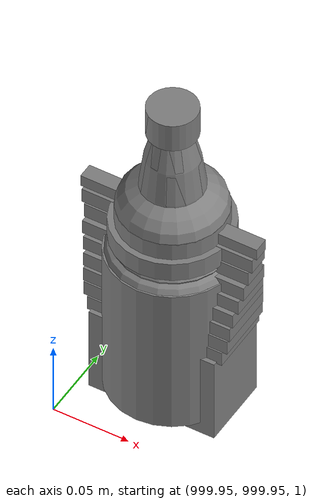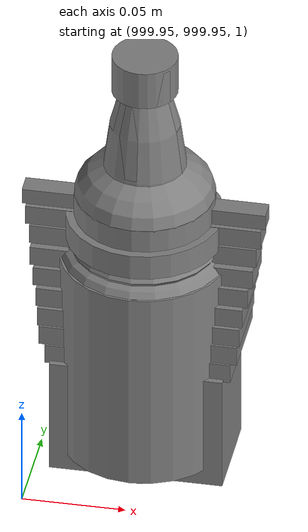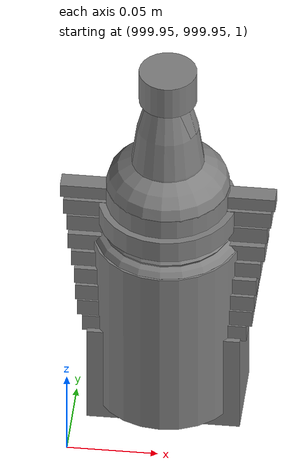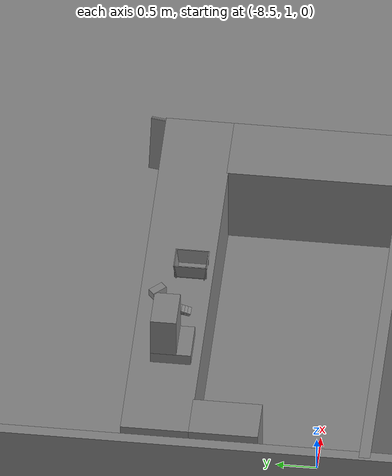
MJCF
<mujoco>
    <option gravity="0.000000000 0.000000000 -9.810000420" timestep="0.0166666" integrator="implicitfast" density="1.225" viscosity="1.8000001e-05" noslip_iterations="10" iterations="100" sdf_iterations="50">
        <flag multiccd="disable"/>
    </option>
    <size memory="1000M"/>
    <compiler coordinate="local"/>
    <worldbody>
        <light cutoff="30" pos="0 1 1" dir="0 -1 -2"/>
        <light cutoff="30" pos="0 -1 1" dir="0 1 -2"/>
        <body pos="0.000000000 0.000000000 0.000000000" euler="0.000000000 0.000000000 0.000000000" name=" Static Objects_ Static Objects">
            <geom contype="1" conaffinity="1" density="1000" type="box" material="" rgba="0.500000000 0.500000000 0.500000000 1.000000000" solimp="0.899999976 0.949999988 0.001000000" friction="1.000000000 0.005000000 0.000100000" solref="0.020000000 1.000000000" margin="0" condim="3" group="0" pos="-3.101639986 6.150595188 1.018643856" quat="1.000000000 0.000000000 0.000000000 0.000000000" size="0.050000001 0.579999983 1.019999981" name=" Static Objects_geom_5E75D400_495C_4C0E_823C_1442B1891B00"/>
            <geom contype="1" conaffinity="1" density="1000" type="box" material="" rgba="0.500000000 0.500000000 0.500000000 1.000000000" solimp="0.899999976 0.949999988 0.001000000" friction="1.000000000 0.005000000 0.000100000" solref="0.020000000 1.000000000" margin="0" condim="3" group="0" pos="-2.825197220 6.153595448 1.115278244" quat="0.707107067 0.000000000 0.000000000 0.707106471" size="0.550000012 0.239999995 0.025000000" name=" Static Objects_geom_88F61B9A_2DD4_49DA_A794_46CC828470B4"/>
            <geom contype="1" conaffinity="1" density="1000" type="box" material="" rgba="0.500000000 0.500000000 0.500000000 1.000000000" solimp="0.899999976 0.949999988 0.001000000" friction="1.000000000 0.005000000 0.000100000" solref="0.020000000 1.000000000" margin="0" condim="3" group="0" pos="-2.825197220 6.153595448 0.097434282" quat="0.707107067 0.000000000 0.000000000 0.707106471" size="0.550000012 0.239999995 0.098999999" name=" Static Objects_geom_1D2FB6C1_D366_4E68_AC9F_3646A76EC579"/>
            <geom contype="1" conaffinity="1" density="1000" type="box" material="" rgba="0.500000000 0.500000000 0.500000000 1.000000000" solimp="0.899999976 0.949999988 0.001000000" friction="1.000000000 0.005000000 0.000100000" solref="0.020000000 1.000000000" margin="0" condim="3" group="0" pos="-6.293097973 6.153595448 1.114443064" quat="0.707107067 0.000000000 0.000000000 0.707106471" size="0.529999971 3.134999990 0.025000000" name=" Static Objects_geom_8D2E067E_5A24_40DB_8A5C_AF866C7020D4"/>
            <geom contype="1" conaffinity="1" density="1000" type="box" material="" rgba="0.500000000 0.500000000 0.500000000 1.000000000" solimp="0.899999976 0.949999988 0.001000000" friction="1.000000000 0.005000000 0.000100000" solref="0.020000000 1.000000000" margin="0" condim="3" group="0" pos="-6.286010742 6.153595448 0.096129179" quat="0.707107067 0.000000000 0.000000000 0.707106471" size="0.529999971 3.134999990 0.098999999" name=" Static Objects_geom_08E78134_F422_4BB2_A1D9_FCD525859733"/>
            <geom contype="1" conaffinity="1" density="1000" type="box" material="" rgba="0.500000000 0.500000000 0.500000000 1.000000000" solimp="0.899999976 0.949999988 0.001000000" friction="1.000000000 0.005000000 0.000100000" solref="0.020000000 1.000000000" margin="0" condim="3" group="0" pos="-2.825197220 6.153595448 1.563861728" quat="0.707107067 0.000000000 0.000000000 0.707106471" size="0.550000012 0.239999995 0.025000000" name=" Static Objects_geom_6AB50E66_9BF5_41D3_B869_9924B21717E6"/>
            <geom contype="1" conaffinity="1" density="1000" type="box" material="" rgba="0.500000000 0.500000000 0.500000000 1.000000000" solimp="0.899999976 0.949999988 0.001000000" friction="1.000000000 0.005000000 0.000100000" solref="0.020000000 1.000000000" margin="0" condim="3" group="0" pos="-6.311686516 6.153595448 1.018643856" quat="0.707107067 0.000000000 0.000000000 0.707106471" size="0.050000001 3.150000095 1.019999981" name=" Static Objects_geom_14DE3F25_C493_4957_869C_E94550E7044A"/>
            <geom contype="1" conaffinity="1" density="1000" type="box" material="" rgba="0.500000000 0.500000000 0.500000000 1.000000000" solimp="0.899999976 0.949999988 0.001000000" friction="1.000000000 0.005000000 0.000100000" solref="0.020000000 1.000000000" margin="0" condim="3" group="0" pos="-2.825197220 6.153595448 0.629031777" quat="0.707107067 0.000000000 0.000000000 0.707106471" size="0.550000012 0.239999995 0.025000000" name=" Static Objects_geom_30E844A1_3525_42F4_A3E3_3E1BD5369A25"/>
            <geom contype="1" conaffinity="1" density="1000" type="box" material="" rgba="0.500000000 0.500000000 0.500000000 1.000000000" solimp="0.899999976 0.949999988 0.001000000" friction="1.000000000 0.005000000 0.000100000" solref="0.020000000 1.000000000" margin="0" condim="3" group="0" pos="-6.286010742 6.153595448 1.563861728" quat="0.707107067 0.000000000 0.000000000 0.707106471" size="0.529999971 3.134999990 0.025000000" name=" Static Objects_geom_69F4C078_74EE_487F_9424_7598F7B57C76"/>
            <geom contype="1" conaffinity="1" density="1000" type="box" material="" rgba="0.500000000 0.500000000 0.500000000 1.000000000" solimp="0.899999976 0.949999988 0.001000000" friction="1.000000000 0.005000000 0.000100000" solref="0.020000000 1.000000000" margin="0" condim="3" group="0" pos="-6.286010742 6.153595448 0.629031777" quat="0.707107067 0.000000000 0.000000000 0.707106471" size="0.529999971 3.134999990 0.025000000" name=" Static Objects_geom_E00F1E3A_2666_443B_950B_2AB06BC0251B"/>
            <geom contype="1" conaffinity="1" density="1000" type="box" material="" rgba="0.500000000 0.500000000 0.500000000 1.000000000" solimp="0.899999976 0.949999988 0.001000000" friction="1.000000000 0.005000000 0.000100000" solref="0.020000000 1.000000000" margin="0" condim="3" group="0" pos="-7.719123363 2.867671013 1.173410416" quat="1.000000000 0.000000000 0.000000000 0.000000000" size="0.250000000 0.250000000 0.079999998" name=" Static Objects_geom_C7DA4803_F1F9_46C8_813E_27EB665E6C3D"/>
            <geom contype="1" conaffinity="1" density="1000" type="box" material="" rgba="0.500000000 0.500000000 0.500000000 1.000000000" solimp="0.899999976 0.949999988 0.001000000" friction="1.000000000 0.005000000 0.000100000" solref="0.020000000 1.000000000" margin="0" condim="3" group="0" pos="-7.408766270 3.088089943 1.776644945" quat="0.928051054 0.000000000 0.000000000 0.372453064" size="0.050000001 0.100000001 0.050000001" name=" Static Objects_geom_35CF67A8_48C2_4EE0_ADFB_A99C1F419F51"/>
            <geom contype="1" conaffinity="1" density="1000" type="box" material="" rgba="0.500000000 0.500000000 0.500000000 1.000000000" solimp="0.899999976 0.949999988 0.001000000" friction="1.000000000 0.005000000 0.000100000" solref="0.020000000 1.000000000" margin="0" condim="3" group="0" pos="-7.719123363 2.958004713 1.530241251" quat="1.000000000 0.000000000 0.000000000 0.000000000" size="0.250000000 0.159999996 0.280000001" name=" Static Objects_geom_6351C23A_E890_4E12_911D_35D532DECF43"/>
            <geom contype="1" conaffinity="1" density="1000" type="cylinder" material="" rgba="0.500000000 0.500000000 0.500000000 1.000000000" solimp="0.899999976 0.949999988 0.001000000" friction="1.000000000 0.005000000 0.000100000" solref="0.020000000 1.000000000" margin="0" condim="3" group="0" pos="-7.427312374 3.069516420 1.502544641" quat="0.928051054 0.000000000 0.000000000 0.372453064" size="0.015000000 0.230000004 0.100000001" name=" Static Objects_geom_A0CCDBFF_CBF1_4E17_8D4B_D991E08A5E5C"/>
            <geom contype="1" conaffinity="1" density="1000" type="box" material="" rgba="0.500000000 0.500000000 0.500000000 1.000000000" solimp="0.899999976 0.949999988 0.001000000" friction="1.000000000 0.005000000 0.000100000" solref="0.020000000 1.000000000" margin="0" condim="3" group="0" pos="-7.437745571 3.067511320 1.289965630" quat="1.000000000 0.000000000 0.000000000 0.000000000" size="0.029999999 0.020000000 0.020000000" name=" Static Objects_geom_5547394A_6E77_4251_A0BC_0B3D8D3B6660"/>
            <geom contype="1" conaffinity="1" density="1000" type="box" material="" rgba="0.500000000 0.500000000 0.500000000 1.000000000" solimp="0.899999976 0.949999988 0.001000000" friction="1.000000000 0.005000000 0.000100000" solref="0.020000000 1.000000000" margin="0" condim="3" group="0" pos="-9.058088303 6.434794426 1.209077358" quat="1.000000000 0.000000000 0.000000000 0.000000000" size="0.250000000 0.100000001 0.070000000" name=" Static Objects_geom_8772A35D_A048_4AC6_A62C_CE05E54119F6"/>
            <geom contype="1" conaffinity="1" density="1000" type="box" material="" rgba="0.500000000 0.500000000 0.500000000 1.000000000" solimp="0.899999976 0.949999988 0.001000000" friction="1.000000000 0.005000000 0.000100000" solref="0.020000000 1.000000000" margin="0" condim="3" group="0" pos="-7.886891365 6.459744930 0.352518857" quat="1.000000000 0.000000000 0.000000000 0.000000000" size="1.500000000 0.200000003 0.150000006" name=" Static Objects_geom_5DF31288_318D_415C_8E08_93C89A12E825"/>
            <geom contype="1" conaffinity="1" density="1000" type="box" material="" rgba="0.500000000 0.500000000 0.500000000 1.000000000" solimp="0.899999976 0.949999988 0.001000000" friction="1.000000000 0.005000000 0.000100000" solref="0.020000000 1.000000000" margin="0" condim="3" group="0" pos="-9.237723351 6.464855671 1.209077358" quat="1.000000000 0.000000000 0.000000000 0.000000000" size="0.100000001 0.100000001 0.070000000" name=" Static Objects_geom_7F4F349F_A870_43F8_B2F1_D1B03FA742BC"/>
            <geom contype="1" conaffinity="1" density="1000" type="box" material="" rgba="0.500000000 0.500000000 0.500000000 1.000000000" solimp="0.899999976 0.949999988 0.001000000" friction="1.000000000 0.005000000 0.000100000" solref="0.020000000 1.000000000" margin="0" condim="3" group="0" pos="-6.924745083 6.362090111 1.214329123" quat="1.000000000 0.000000000 0.000000000 0.000000000" size="0.200000003 0.100000001 0.075000003" name=" Static Objects_geom_A08C0BED_7A5A_4696_A5C9_225E58A75564"/>
            <geom contype="1" conaffinity="1" density="1000" type="box" material="" rgba="0.500000000 0.500000000 0.500000000 1.000000000" solimp="0.899999976 0.949999988 0.001000000" friction="1.000000000 0.005000000 0.000100000" solref="0.020000000 1.000000000" margin="0" condim="3" group="0" pos="-4.407354832 6.459744930 1.292199373" quat="1.000000000 0.000000000 0.000000000 0.000000000" size="1.240000010 0.200000003 0.150000006" name=" Static Objects_geom_AE30EB52_7EEE_4494_B76A_9A008729628A"/>
            <geom contype="1" conaffinity="1" density="1000" type="box" material="" rgba="0.500000000 0.500000000 0.500000000 1.000000000" solimp="0.899999976 0.949999988 0.001000000" friction="1.000000000 0.005000000 0.000100000" solref="0.020000000 1.000000000" margin="0" condim="3" group="0" pos="-5.611940861 6.318420410 0.350975692" quat="1.000000000 0.000000000 0.000000000 0.000000000" size="0.699999988 0.100000001 0.150000006" name=" Static Objects_geom_3BBF0633_3227_466F_9ED5_62DFF4DE65CA"/>
            <geom contype="1" conaffinity="1" density="1000" type="box" material="" rgba="0.500000000 0.500000000 0.500000000 1.000000000" solimp="0.899999976 0.949999988 0.001000000" friction="1.000000000 0.005000000 0.000100000" solref="0.020000000 1.000000000" margin="0" condim="3" group="0" pos="-6.300771236 6.459744930 1.744376063" quat="1.000000000 0.000000000 0.000000000 0.000000000" size="3.000000000 0.200000003 0.150000006" name=" Static Objects_geom_4AA922DD_0FBA_480A_9547_A23AA072F3A1"/>
            <geom contype="1" conaffinity="1" density="1000" type="box" material="" rgba="0.500000000 0.500000000 0.500000000 1.000000000" solimp="0.899999976 0.949999988 0.001000000" friction="1.000000000 0.005000000 0.000100000" solref="0.020000000 1.000000000" margin="0" condim="3" group="0" pos="-6.751636982 6.459744930 0.800981164" quat="1.000000000 0.000000000 0.000000000 0.000000000" size="2.200000048 0.200000003 0.150000006" name=" Static Objects_geom_3FE6A83D_FC86_4E12_A1DA_699AFE3F22BF"/>
            <geom contype="1" conaffinity="1" density="1000" type="box" material="" rgba="0.500000000 0.500000000 0.500000000 1.000000000" solimp="0.899999976 0.949999988 0.001000000" friction="1.000000000 0.005000000 0.000100000" solref="0.020000000 1.000000000" margin="0" condim="3" group="0" pos="-8.844120979 6.464855671 1.209077358" quat="1.000000000 0.000000000 0.000000000 0.000000000" size="0.100000001 0.100000001 0.070000000" name=" Static Objects_geom_4F0C3788_6D32_41BE_9B08_2A6DCA0EC698"/>
            <geom contype="1" conaffinity="1" density="1000" type="box" material="" rgba="0.500000000 0.500000000 0.500000000 1.000000000" solimp="0.899999976 0.949999988 0.001000000" friction="1.000000000 0.005000000 0.000100000" solref="0.020000000 1.000000000" margin="0" condim="3" group="0" pos="-6.098561764 6.327973843 1.292199373" quat="1.000000000 0.000000000 0.000000000 0.000000000" size="0.500000000 0.100000001 0.150000006" name=" Static Objects_geom_3843F71E_6151_4B3E_9552_511EE92960C8"/>
            <geom contype="1" conaffinity="1" density="1000" type="box" material="" rgba="0.500000000 0.500000000 0.500000000 1.000000000" solimp="0.899999976 0.949999988 0.001000000" friction="1.000000000 0.005000000 0.000100000" solref="0.020000000 1.000000000" margin="0" condim="3" group="0" pos="-6.824534416 6.447464466 1.212718010" quat="1.000000000 0.000000000 0.000000000 0.000000000" size="0.100000001 0.100000001 0.075000003" name=" Static Objects_geom_AF83A4CF_3F9B_4849_B642_E27EFB4B76E0"/>
            <geom contype="1" conaffinity="1" density="1000" type="box" material="" rgba="0.500000000 0.500000000 0.500000000 1.000000000" solimp="0.899999976 0.949999988 0.001000000" friction="1.000000000 0.005000000 0.000100000" solref="0.020000000 1.000000000" margin="0" condim="3" group="0" pos="-3.907610416 6.318625927 0.800981164" quat="1.000000000 0.000000000 0.000000000 0.000000000" size="0.500000000 0.100000001 0.150000006" name=" Static Objects_geom_0EADBE96_2E73_4465_9B1D_106BBCDD3F3A"/>
            <geom contype="1" conaffinity="1" density="1000" type="box" material="" rgba="0.500000000 0.500000000 0.500000000 1.000000000" solimp="0.899999976 0.949999988 0.001000000" friction="1.000000000 0.005000000 0.000100000" solref="0.020000000 1.000000000" margin="0" condim="3" group="0" pos="-7.373087406 6.458900928 1.214329123" quat="1.000000000 0.000000000 0.000000000 0.000000000" size="0.250000000 0.200000003 0.075000003" name=" Static Objects_geom_A47A3885_E6E9_4400_B56E_84B38813EF90"/>
            <geom contype="1" conaffinity="1" density="1000" type="box" material="" rgba="0.500000000 0.500000000 0.500000000 1.000000000" solimp="0.899999976 0.949999988 0.001000000" friction="1.000000000 0.005000000 0.000100000" solref="0.020000000 1.000000000" margin="0" condim="3" group="0" pos="-4.035642624 6.459744930 0.352518857" quat="1.000000000 0.000000000 0.000000000 0.000000000" size="0.800000012 0.200000003 0.150000006" name=" Static Objects_geom_2E9191B8_615C_4C4A_9BD6_2DA2BAB51CBB"/>
            <geom contype="1" conaffinity="1" density="1000" type="box" material="" rgba="0.500000000 0.500000000 0.500000000 1.000000000" solimp="0.899999976 0.949999988 0.001000000" friction="1.000000000 0.005000000 0.000100000" solref="0.020000000 1.000000000" margin="0" condim="3" group="0" pos="-6.460197449 2.937205315 0.548931718" quat="1.000000000 0.000000000 0.000000000 0.000000000" size="2.650000095 0.430000007 0.550000012" name=" Static Objects_geom_E8A86131_9635_4D67_BF03_25724F151426"/>
            <geom contype="1" conaffinity="1" density="1000" type="box" material="" rgba="0.500000000 0.500000000 0.500000000 1.000000000" solimp="0.899999976 0.949999988 0.001000000" friction="1.000000000 0.005000000 0.000100000" solref="0.020000000 1.000000000" margin="0" condim="3" group="0" pos="-4.240264893 1.327049494 0.549888909" quat="1.000000000 0.000000000 0.000000000 0.000000000" size="0.430000007 1.200000048 0.550000012" name=" Static Objects_geom_C5BB2546_2B3D_4D88_9C11_94B80722D0EF"/>
            <geom contype="1" conaffinity="1" density="1000" type="box" material="" rgba="0.500000000 0.500000000 0.500000000 1.000000000" solimp="0.899999976 0.949999988 0.001000000" friction="1.000000000 0.005000000 0.000100000" solref="0.020000000 1.000000000" margin="0" condim="3" group="0" pos="-8.830721855 2.096410990 0.549305558" quat="1.000000000 0.000000000 0.000000000 0.000000000" size="0.280000001 0.430000007 0.550000012" name=" Static Objects_geom_DD03A288_BE9B_4742_B0FD_122D38873A95"/>
            <geom contype="1" conaffinity="1" density="1000" type="plane" material="" rgba="0.500000000 0.500000000 0.500000000 1.000000000" solimp="0.899999976 0.949999988 0.001000000" friction="1.000000000 0.005000000 0.000100000" solref="0.020000000 1.000000000" margin="0" condim="3" group="0" pos="-6.000000000 10.399999619 0.000000000" quat="1.000000000 0.000000000 0.000000000 0.000000000" size="6.050000191 10.800000191 0.010000000" name=" Static Objects_geom_E2EA8420_D8F6_477C_82C7_917A8341896D"/>
            <geom contype="1" conaffinity="1" density="1000" type="box" material="" rgba="0.500000000 0.500000000 0.500000000 1.000000000" solimp="0.899999976 0.949999988 0.001000000" friction="1.000000000 0.005000000 0.000100000" solref="0.020000000 1.000000000" margin="0" condim="3" group="0" pos="-6.000000000 0.035000000 2.000000000" quat="1.000000000 0.000000000 0.000000000 0.000000000" size="6.079999924 0.070000000 2.000000000" name=" Static Objects_geom_4B1493D2_A590_46B0_B56D_4320217572E2"/>
            <geom contype="1" conaffinity="1" density="1000" type="box" material="" rgba="0.500000000 0.500000000 0.500000000 1.000000000" solimp="0.899999976 0.949999988 0.001000000" friction="1.000000000 0.005000000 0.000100000" solref="0.020000000 1.000000000" margin="0" condim="3" group="0" pos="-6.000000000 20.159999847 2.000000000" quat="1.000000000 0.000000000 0.000000000 0.000000000" size="6.079999924 0.070000000 2.000000000" name=" Static Objects_geom_FD1483F1_BE95_45D0_9459_34473E2E8890"/>
            <geom contype="1" conaffinity="1" density="1000" type="box" material="" rgba="0.500000000 0.500000000 0.500000000 1.000000000" solimp="0.899999976 0.949999988 0.001000000" friction="1.000000000 0.005000000 0.000100000" solref="0.020000000 1.000000000" margin="0" condim="3" group="0" pos="0.000000000 10.000000000 2.000000000" quat="1.000000000 0.000000000 0.000000000 0.000000000" size="0.070000000 10.500000000 2.000000000" name=" Static Objects_geom_44D3642A_06AB_4110_9198_64015D4888CB"/>
            <geom contype="1" conaffinity="1" density="1000" type="box" material="" rgba="0.500000000 0.500000000 0.500000000 1.000000000" solimp="0.899999976 0.949999988 0.001000000" friction="1.000000000 0.005000000 0.000100000" solref="0.020000000 1.000000000" margin="0" condim="3" group="0" pos="-12.050000191 10.000000000 2.000000000" quat="1.000000000 0.000000000 0.000000000 0.000000000" size="0.070000000 10.500000000 2.000000000" name=" Static Objects_geom_4CD7925E_B8F0_48FB_874C_2171BC5EE9F7"/>
        </body>
        <body pos="1000.000000000 1000.000000000 1.000000000" euler="0.000000000 0.000000000 0.000000000" name="openloong_gripper_2f85_fix_base_usda_salt">
            <geom contype="1" conaffinity="1" density="1000" type="box" material="" rgba="0.500000000 0.500000000 0.500000000 1.000000000" solimp="0.899999976 0.949999988 0.001000000" friction="1.000000000 0.005000000 0.000100000" solref="0.020000000 1.000000000" margin="0" condim="3" group="0" pos="0.000305176 0.000000000 0.084862232" quat="1.000000000 0.000000000 0.000000000 0.000000000" size="0.048999999 0.018999999 0.005000000" name="openloong_gripper_2f85_fix_base_usda_geom_BB66C232_6B21_47DD_BD85_0A48E3EB1C03"/>
            <geom contype="1" conaffinity="1" density="1000" type="box" material="" rgba="0.500000000 0.500000000 0.500000000 1.000000000" solimp="0.899999976 0.949999988 0.001000000" friction="1.000000000 0.005000000 0.000100000" solref="0.020000000 1.000000000" margin="0" condim="3" group="0" pos="0.000305176 0.000000000 0.104564309" quat="1.000000000 0.000000000 0.000000000 0.000000000" size="0.052000001 0.014000000 0.005000000" name="openloong_gripper_2f85_fix_base_usda_geom_1A427C68_D288_4404_BC82_AFD36AFAE263"/>
            <geom contype="1" conaffinity="1" density="1000" type="box" material="" rgba="0.500000000 0.500000000 0.500000000 1.000000000" solimp="0.899999976 0.949999988 0.001000000" friction="1.000000000 0.005000000 0.000100000" solref="0.020000000 1.000000000" margin="0" condim="3" group="0" pos="0.000305176 0.000000000 0.114487171" quat="1.000000000 0.000000000 0.000000000 0.000000000" size="0.054000001 0.011500000 0.005000000" name="openloong_gripper_2f85_fix_base_usda_geom_7FE5BE96_FAB6_424D_AAD8_FCBF0BC863ED"/>
            <geom contype="1" conaffinity="1" density="1000" type="box" material="" rgba="0.500000000 0.500000000 0.500000000 1.000000000" solimp="0.899999976 0.949999988 0.001000000" friction="1.000000000 0.005000000 0.000100000" solref="0.020000000 1.000000000" margin="0" condim="3" group="0" pos="0.000305176 0.000000000 0.075103164" quat="1.000000000 0.000000000 0.000000000 0.000000000" size="0.048000000 0.020000000 0.005000000" name="openloong_gripper_2f85_fix_base_usda_geom_55D9DD63_9F7E_4004_B599_3D155E890D83"/>
            <geom contype="1" conaffinity="1" density="1000" type="box" material="" rgba="0.500000000 0.500000000 0.500000000 1.000000000" solimp="0.899999976 0.949999988 0.001000000" friction="1.000000000 0.005000000 0.000100000" solref="0.020000000 1.000000000" margin="0" condim="3" group="0" pos="0.000305176 0.000000000 0.134892464" quat="1.000000000 0.000000000 0.000000000 0.000000000" size="0.057000000 0.007000000 0.005000000" name="openloong_gripper_2f85_fix_base_usda_geom_8937B499_4518_4CF2_AD30_A872788F392B"/>
            <geom contype="1" conaffinity="1" density="1000" type="box" material="" rgba="0.500000000 0.500000000 0.500000000 1.000000000" solimp="0.899999976 0.949999988 0.001000000" friction="1.000000000 0.005000000 0.000100000" solref="0.020000000 1.000000000" margin="0" condim="3" group="0" pos="0.000305176 0.000000000 0.094920278" quat="1.000000000 0.000000000 0.000000000 0.000000000" size="0.050000001 0.017000001 0.005000000" name="openloong_gripper_2f85_fix_base_usda_geom_89064913_1C8E_4121_8CDB_53F064F6949A"/>
            <geom contype="1" conaffinity="1" density="1000" type="box" material="" rgba="0.500000000 0.500000000 0.500000000 1.000000000" solimp="0.899999976 0.949999988 0.001000000" friction="1.000000000 0.005000000 0.000100000" solref="0.020000000 1.000000000" margin="0" condim="3" group="0" pos="0.000305176 0.000000000 0.065204859" quat="1.000000000 0.000000000 0.000000000 0.000000000" size="0.045000002 0.021000000 0.005000000" name="openloong_gripper_2f85_fix_base_usda_geom_6158D957_D0F2_428F_92AB_5FEC79B4F919"/>
            <geom contype="1" conaffinity="1" density="1000" type="box" material="" rgba="0.500000000 0.500000000 0.500000000 1.000000000" solimp="0.899999976 0.949999988 0.001000000" friction="1.000000000 0.005000000 0.000100000" solref="0.020000000 1.000000000" margin="0" condim="3" group="0" pos="0.000305176 0.000000000 0.144135714" quat="1.000000000 0.000000000 0.000000000 0.000000000" size="0.059000000 0.005000000 0.004000000" name="openloong_gripper_2f85_fix_base_usda_geom_5D5C0710_2424_4FB7_B0B7_5F646E535DC0"/>
            <geom contype="1" conaffinity="1" density="1000" type="box" material="" rgba="0.500000000 0.500000000 0.500000000 1.000000000" solimp="0.899999976 0.949999988 0.001000000" friction="1.000000000 0.005000000 0.000100000" solref="0.020000000 1.000000000" margin="0" condim="3" group="0" pos="0.000000000 0.000000000 0.031593561" quat="1.000000000 0.000000000 0.000000000 0.000000000" size="0.041999999 0.024000000 0.029999999" name="openloong_gripper_2f85_fix_base_usda_geom_0C7140EF_1E85_49A9_BD8E_E339413FEDB5"/>
            <geom contype="1" conaffinity="1" density="1000" type="box" material="" rgba="0.500000000 0.500000000 0.500000000 1.000000000" solimp="0.899999976 0.949999988 0.001000000" friction="1.000000000 0.005000000 0.000100000" solref="0.020000000 1.000000000" margin="0" condim="3" group="0" pos="0.000305176 0.000000000 0.124608755" quat="1.000000000 0.000000000 0.000000000 0.000000000" size="0.055000000 0.008000000 0.005000000" name="openloong_gripper_2f85_fix_base_usda_geom_18679163_8718_41EF_BBCA_FA5DBB52C21E"/>
            <freejoint name="openloong_gripper_2f85_fix_base_usda_salt_joint"/>
            <site size="0.005000000 0.005000000 0.005000000" rgba="0.500000000 0.500000000 0.500000000 1.000000000" pos="0.000000000 0.000000000 0.000000000" quat="1.000000000 0.000000000 0.000000000 0.000000000" group="0" type="sphere" name="openloong_gripper_2f85_fix_base_usda_saltsite"/>
        </body>
        <body pos="1000.000000000 1000.000000000 1.000000000" euler="0.000000000 0.000000000 0.000000000" name="openloong_gripper_2f85_fix_base_usda_can">
            <geom contype="1" conaffinity="1" density="1000" type="cylinder" material="" rgba="0.500000000 0.500000000 0.500000000 1.000000000" solimp="0.899999976 0.949999988 0.001000000" friction="1.000000000 0.005000000 0.000100000" solref="0.020000000 1.000000000" margin="0" condim="3" group="0" pos="0.000000000 0.000000000 0.079676986" quat="1.000000000 0.000000000 0.000000000 0.000000000" size="0.034000002 0.071999997 1.000000000" name="openloong_gripper_2f85_fix_base_usda_geom_06F5B281_35FA_425F_BBE2_4E2CF8CBB753"/>
            <geom contype="1" conaffinity="1" density="1000" type="ellipsoid" material="" rgba="0.500000000 0.500000000 0.500000000 1.000000000" solimp="0.899999976 0.949999988 0.001000000" friction="1.000000000 0.005000000 0.000100000" solref="0.020000000 1.000000000" margin="0" condim="3" group="0" pos="0.000000000 0.000000000 0.151854277" quat="1.000000000 0.000000000 0.000000000 0.000000000" size="0.034000002 0.034000002 0.020000000" name="openloong_gripper_2f85_fix_base_usda_geom_A863480B_87A9_4215_90BF_E9B8EFE99CD0"/>
            <geom contype="1" conaffinity="1" density="1000" type="box" material="" rgba="0.500000000 0.500000000 0.500000000 1.000000000" solimp="0.899999976 0.949999988 0.001000000" friction="1.000000000 0.005000000 0.000100000" solref="0.020000000 1.000000000" margin="0" condim="3" group="0" pos="0.000000000 0.000000000 0.004777670" quat="1.000000000 0.000000000 0.000000000 0.000000000" size="0.020000000 0.020000000 0.005000000" name="openloong_gripper_2f85_fix_base_usda_geom_00BE303D_CE6B_4D94_8314_DA3530DB4EFE"/>
            <freejoint name="openloong_gripper_2f85_fix_base_usda_can_joint"/>
            <site size="0.005000000 0.005000000 0.005000000" rgba="0.500000000 0.500000000 0.500000000 1.000000000" pos="0.000000000 0.000000000 0.000000000" quat="1.000000000 0.000000000 0.000000000 0.000000000" group="0" type="sphere" name="openloong_gripper_2f85_fix_base_usda_cansite"/>
        </body>
        <body pos="1000.000000000 1000.000000000 1.000000000" euler="0.000000000 0.000000000 0.000000000" name="openloong_gripper_2f85_fix_base_usda_bottle_blue">
            <geom contype="1" conaffinity="1" density="1000" type="ellipsoid" material="" rgba="0.500000000 0.500000000 0.500000000 1.000000000" solimp="0.899999976 0.949999988 0.001000000" friction="1.000000000 0.005000000 0.000100000" solref="0.020000000 1.000000000" margin="0" condim="3" group="0" pos="0.000000000 0.000000000 0.118920922" quat="1.000000000 0.000000000 0.000000000 0.000000000" size="0.030999999 0.030999999 0.029999999" name="openloong_gripper_2f85_fix_base_usda_geom_4A01FB9F_1F4B_4C45_A939_1D2CD23D208F"/>
            <geom contype="1" conaffinity="1" density="1000" type="box" material="" rgba="0.500000000 0.500000000 0.500000000 1.000000000" solimp="0.899999976 0.949999988 0.001000000" friction="1.000000000 0.005000000 0.000100000" solref="0.020000000 1.000000000" margin="0" condim="3" group="0" pos="0.000000000 0.000000000 0.002164602" quat="1.000000000 0.000000000 0.000000000 0.000000000" size="0.020000000 0.020000000 0.003000000" name="openloong_gripper_2f85_fix_base_usda_geom_7B8CEA78_A33A_488E_A400_056BBBBBDF10"/>
            <geom contype="1" conaffinity="1" density="1000" type="cylinder" material="" rgba="0.500000000 0.500000000 0.500000000 1.000000000" solimp="0.899999976 0.949999988 0.001000000" friction="1.000000000 0.005000000 0.000100000" solref="0.020000000 1.000000000" margin="0" condim="3" group="0" pos="0.000000000 -0.000366211 0.060859680" quat="1.000000000 0.000000000 0.000000000 0.000000000" size="0.030999999 0.057999998 1.000000000" name="openloong_gripper_2f85_fix_base_usda_geom_332E54DA_351F_441E_81B3_7AB6C7157D25"/>
            <geom contype="1" conaffinity="1" density="1000" type="cylinder" material="" rgba="0.500000000 0.500000000 0.500000000 1.000000000" solimp="0.899999976 0.949999988 0.001000000" friction="1.000000000 0.005000000 0.000100000" solref="0.020000000 1.000000000" margin="0" condim="3" group="0" pos="0.000000000 0.000000000 0.220594406" quat="1.000000000 0.000000000 0.000000000 0.000000000" size="0.016000001 0.010000000 1.000000000" name="openloong_gripper_2f85_fix_base_usda_geom_A763E11A_95F5_4EEC_ADF0_58FE04DD1A0F"/>
            <geom contype="1" conaffinity="1" density="1000" type="ellipsoid" material="" rgba="0.500000000 0.500000000 0.500000000 1.000000000" solimp="0.899999976 0.949999988 0.001000000" friction="1.000000000 0.005000000 0.000100000" solref="0.020000000 1.000000000" margin="0" condim="3" group="0" pos="0.000000000 0.000000000 0.144259930" quat="1.000000000 0.000000000 0.000000000 0.000000000" size="0.021000000 0.021000000 0.079999998" name="openloong_gripper_2f85_fix_base_usda_geom_49C9B1EA_1A83_44F9_8930_B39B34823EF8"/>
            <freejoint name="openloong_gripper_2f85_fix_base_usda_bottle_blue_joint"/>
            <site size="0.005000000 0.005000000 0.005000000" rgba="0.500000000 0.500000000 0.500000000 1.000000000" pos="0.000000000 0.000000000 0.000000000" quat="0.999961913 0.008726535 0.000000000 0.000000000" group="0" type="sphere" name="openloong_gripper_2f85_fix_base_usda_bottle_bluesite"/>
        </body>
        <body pos="-1.816719770 6.167973042 1.800594807" euler="-130.354278564 -11.079745293 167.347717285" mocap="true" name="spotlight1_SpotLight"/>
        <body pos="-1.872589469 6.446184635 1.675997257" euler="138.536972046 73.404258728 -36.501144409" mocap="true" name="spotlight4_SpotLight"/>
        <body pos="1000.000000000 1000.000000000 1.000000000" euler="0.000000000 0.000000000 0.000000000" name="openloong_gripper_2f85_fix_base_usda_bottle_red">
            <geom contype="1" conaffinity="1" density="1000" type="ellipsoid" material="" rgba="0.500000000 0.500000000 0.500000000 1.000000000" solimp="0.899999976 0.949999988 0.001000000" friction="1.000000000 0.005000000 0.000100000" solref="0.020000000 1.000000000" margin="0" condim="3" group="0" pos="0.000000000 0.000000000 0.144284487" quat="1.000000000 0.000000000 0.000000000 0.000000000" size="0.021000000 0.021000000 0.079999998" name="openloong_gripper_2f85_fix_base_usda_geom_6E700C96_1DB1_4486_A93B_7F3735A22599"/>
            <geom contype="1" conaffinity="1" density="1000" type="cylinder" material="" rgba="0.500000000 0.500000000 0.500000000 1.000000000" solimp="0.899999976 0.949999988 0.001000000" friction="1.000000000 0.005000000 0.000100000" solref="0.020000000 1.000000000" margin="0" condim="3" group="0" pos="0.000000000 0.000000000 0.220618963" quat="1.000000000 0.000000000 0.000000000 0.000000000" size="0.016000001 0.010000000 1.000000000" name="openloong_gripper_2f85_fix_base_usda_geom_6AE208D5_249D_415F_A491_2A3397951E4A"/>
            <geom contype="1" conaffinity="1" density="1000" type="ellipsoid" material="" rgba="0.500000000 0.500000000 0.500000000 1.000000000" solimp="0.899999976 0.949999988 0.001000000" friction="1.000000000 0.005000000 0.000100000" solref="0.020000000 1.000000000" margin="0" condim="3" group="0" pos="0.000000000 0.000000000 0.118945479" quat="1.000000000 0.000000000 0.000000000 0.000000000" size="0.030999999 0.030999999 0.029999999" name="openloong_gripper_2f85_fix_base_usda_geom_508E6E37_53D0_4321_AC1D_3299006F9047"/>
            <geom contype="1" conaffinity="1" density="1000" type="box" material="" rgba="0.500000000 0.500000000 0.500000000 1.000000000" solimp="0.899999976 0.949999988 0.001000000" friction="1.000000000 0.005000000 0.000100000" solref="0.020000000 1.000000000" margin="0" condim="3" group="0" pos="0.000000000 0.000000000 0.002189159" quat="1.000000000 0.000000000 0.000000000 0.000000000" size="0.020000000 0.020000000 0.003000000" name="openloong_gripper_2f85_fix_base_usda_geom_96803558_C2EB_4A4A_919C_08614A4431AE"/>
            <geom contype="1" conaffinity="1" density="1000" type="cylinder" material="" rgba="0.500000000 0.500000000 0.500000000 1.000000000" solimp="0.899999976 0.949999988 0.001000000" friction="1.000000000 0.005000000 0.000100000" solref="0.020000000 1.000000000" margin="0" condim="3" group="0" pos="0.000000000 -0.000366211 0.060884237" quat="1.000000000 0.000000000 0.000000000 0.000000000" size="0.030999999 0.057999998 1.000000000" name="openloong_gripper_2f85_fix_base_usda_geom_23D85A19_4802_4949_8488_C9238623B0CD"/>
            <freejoint name="openloong_gripper_2f85_fix_base_usda_bottle_red_joint"/>
            <site size="0.005000000 0.005000000 0.005000000" rgba="0.500000000 0.500000000 0.500000000 1.000000000" pos="0.000000000 0.000000000 0.000000000" quat="0.999961913 0.008726535 0.000000000 0.000000000" group="0" type="sphere" name="openloong_gripper_2f85_fix_base_usda_bottle_redsite"/>
        </body>
        <body pos="-2.333895683 6.047860146 1.800318360" euler="-58.224491119 70.092575073 41.433280945" mocap="true" name="spotlight6_SpotLight"/>
        <body pos="1000.000000000 1000.000000000 1.000000000" euler="0.000000000 0.000000000 0.000000000" name="openloong_gripper_2f85_fix_base_usda_jar_01">
            <geom contype="1" conaffinity="1" density="1000" type="box" material="" rgba="0.500000000 0.500000000 0.500000000 1.000000000" solimp="0.899999976 0.949999988 0.001000000" friction="1.000000000 0.005000000 0.000100000" solref="0.020000000 1.000000000" margin="0" condim="3" group="0" pos="0.000000000 0.000000000 0.006158113" quat="1.000000000 0.000000000 0.000000000 0.000000000" size="0.020000000 0.020000000 0.005000000" name="openloong_gripper_2f85_fix_base_usda_geom_C8F4534B_0AF4_452F_8ACA_B3088E47C599"/>
            <geom contype="1" conaffinity="1" density="1000" type="cylinder" material="" rgba="0.500000000 0.500000000 0.500000000 1.000000000" solimp="0.899999976 0.949999988 0.001000000" friction="1.000000000 0.005000000 0.000100000" solref="0.020000000 1.000000000" margin="0" condim="3" group="0" pos="0.000000000 0.000000000 0.062744498" quat="1.000000000 0.000000000 0.000000000 0.000000000" size="0.041000001 0.052999999 1.000000000" name="openloong_gripper_2f85_fix_base_usda_geom_B4413BB0_6232_4A80_9135_7B3F3A0631E9"/>
            <geom contype="1" conaffinity="1" density="1000" type="ellipsoid" material="" rgba="0.500000000 0.500000000 0.500000000 1.000000000" solimp="0.899999976 0.949999988 0.001000000" friction="1.000000000 0.005000000 0.000100000" solref="0.020000000 1.000000000" margin="0" condim="3" group="0" pos="0.000000000 0.000000000 0.122252703" quat="1.000000000 0.000000000 0.000000000 0.000000000" size="0.035999998 0.035999998 0.010000000" name="openloong_gripper_2f85_fix_base_usda_geom_5C687E8C_EAA9_419A_88FB_CAB6C961E0BE"/>
            <geom contype="1" conaffinity="1" density="1000" type="cylinder" material="" rgba="0.500000000 0.500000000 0.500000000 1.000000000" solimp="0.899999976 0.949999988 0.001000000" friction="1.000000000 0.005000000 0.000100000" solref="0.020000000 1.000000000" margin="0" condim="3" group="0" pos="0.000000000 0.000000000 0.015747190" quat="1.000000000 0.000000000 0.000000000 0.000000000" size="0.035000000 0.010000000 1.000000000" name="openloong_gripper_2f85_fix_base_usda_geom_653D61B3_354B_46C0_9F25_774E7B39C71A"/>
            <geom contype="1" conaffinity="1" density="1000" type="ellipsoid" material="" rgba="0.500000000 0.500000000 0.500000000 1.000000000" solimp="0.899999976 0.949999988 0.001000000" friction="1.000000000 0.005000000 0.000100000" solref="0.020000000 1.000000000" margin="0" condim="3" group="0" pos="0.000000000 0.000000000 0.115815401" quat="1.000000000 0.000000000 0.000000000 0.000000000" size="0.039999999 0.039999999 0.010000000" name="openloong_gripper_2f85_fix_base_usda_geom_440CB686_7BF6_4A53_B02A_4DA104FA714D"/>
            <geom contype="1" conaffinity="1" density="1000" type="cylinder" material="" rgba="0.500000000 0.500000000 0.500000000 1.000000000" solimp="0.899999976 0.949999988 0.001000000" friction="1.000000000 0.005000000 0.000100000" solref="0.020000000 1.000000000" margin="0" condim="3" group="0" pos="0.000000000 0.000000000 0.133183479" quat="1.000000000 0.000000000 0.000000000 0.000000000" size="0.037999999 0.006500000 1.000000000" name="openloong_gripper_2f85_fix_base_usda_geom_C00E879B_F21A_4828_8D82_D77D0C60E5CF"/>
            <freejoint name="openloong_gripper_2f85_fix_base_usda_jar_01_joint"/>
            <site size="0.005000000 0.005000000 0.005000000" rgba="0.500000000 0.500000000 0.500000000 1.000000000" pos="0.000000000 0.000000000 0.000000000" quat="1.000000000 0.000000000 0.000000000 0.000000000" group="0" type="sphere" name="openloong_gripper_2f85_fix_base_usda_jar_01site"/>
        </body>
        <body pos="0.000000000 0.000000000 0.000000000" euler="0.000000000 0.000000000 0.000000000" name="Interactive Objects_Interactive Objects"/>
        <body pos="-3.510578632 3.403555870 -0.000000100" euler="0.000000000 0.000000000 40.200675964" name="openloong_gripper_2f85_fix_base_usda_PZ">
            <geom contype="1" conaffinity="1" density="1000" type="box" material="" rgba="0.500000000 0.500000000 0.500000000 1.000000000" solimp="0.899999976 0.949999988 0.001000000" friction="1.000000000 0.005000000 0.000100000" solref="0.020000000 1.000000000" margin="0" condim="3" group="0" pos="-0.047453165 0.056484699 0.373715430" quat="0.934750080 0.077914521 0.028795123 0.345459938" size="0.180000007 0.010000000 0.379999995" name="openloong_gripper_2f85_fix_base_usda_geom_5A43068C_23F6_412A_8BAA_E5D55C0CB3EE"/>
            <geom contype="1" conaffinity="1" density="1000" type="box" material="" rgba="0.500000000 0.500000000 0.500000000 1.000000000" solimp="0.899999976 0.949999988 0.001000000" friction="1.000000000 0.005000000 0.000100000" solref="0.020000000 1.000000000" margin="0" condim="3" group="0" pos="0.047452450 -0.054376602 0.374072611" quat="0.934387863 -0.082143910 -0.030358355 0.345326364" size="0.180000007 0.010000000 0.379999995" name="openloong_gripper_2f85_fix_base_usda_geom_F6283DB8_C38C_43E7_B12F_3CEE72168327"/>
            <freejoint name="openloong_gripper_2f85_fix_base_usda_PZ"/>
        </body>
        <body pos="-6.332345009 2.779978037 1.034067392" euler="0.000000000 0.000000000 0.000000000" name="openloong_gripper_2f85_fix_base_usda_basket">
            <geom contype="1" conaffinity="1" density="100000" type="box" material="" rgba="0.500000000 0.500000000 0.500000000 1.000000000" solimp="0.899999976 0.949999988 0.001000000" friction="1.000000000 0.899999976 0.000100000" solref="0.020000000 1.000000000" margin="0" condim="3" group="0" pos="-0.172339439 0.000000000 0.168361664" quat="0.706172407 -0.036353018 -0.036353093 0.706170976" size="0.200000003 0.006000000 0.108000003" name="openloong_gripper_2f85_fix_base_usda_geom_A46D90F0_73E6_4A1A_93EC_2F94B324D05A"/>
            <geom contype="1" conaffinity="1" density="100000" type="box" material="" rgba="0.500000000 0.500000000 0.500000000 1.000000000" solimp="0.899999976 0.949999988 0.001000000" friction="1.000000000 0.899999976 0.000100000" solref="0.020000000 1.000000000" margin="0" condim="3" group="0" pos="-0.039724827 -0.188568115 0.167089701" quat="0.997537494 0.070135131 0.000000000 0.000000000" size="0.150000006 0.006000000 0.108000003" name="openloong_gripper_2f85_fix_base_usda_geom_91302FEB_F7EA_4F51_A74F_5A8C58326343"/>
            <geom contype="1" conaffinity="1" density="100000" type="box" material="" rgba="0.500000000 0.500000000 0.500000000 1.000000000" solimp="0.899999976 0.949999988 0.001000000" friction="1.000000000 0.899999976 0.000100000" solref="0.020000000 1.000000000" margin="0" condim="3" group="0" pos="-0.039724827 0.188377380 0.167089701" quat="0.997489929 -0.070808925 0.000000000 0.000000000" size="0.150000006 0.006000000 0.108000003" name="openloong_gripper_2f85_fix_base_usda_geom_652FACB3_8EA6_4E7A_8144_2A2549D61279"/>
            <geom contype="1" conaffinity="1" density="100000" type="box" material="" rgba="0.500000000 0.500000000 0.500000000 1.000000000" solimp="0.899999976 0.949999988 0.001000000" friction="1.000000000 0.899999976 0.000100000" solref="0.020000000 1.000000000" margin="0" condim="3" group="0" pos="-0.039724827 0.000000000 0.068126202" quat="1.000000000 0.000000000 0.000000000 0.000000000" size="0.129999995 0.174999997 0.006000000" name="openloong_gripper_2f85_fix_base_usda_geom_3B1ABBAD_ADFC_4025_93A0_9021DFEF25BF"/>
            <geom contype="1" conaffinity="1" density="100000" type="box" material="" rgba="0.500000000 0.500000000 0.500000000 1.000000000" solimp="0.899999976 0.949999988 0.001000000" friction="1.000000000 0.899999976 0.000100000" solref="0.020000000 1.000000000" margin="0" condim="3" group="0" pos="0.094372749 0.000000000 0.168361664" quat="0.706172049 0.036353335 0.036353379 0.706171215" size="0.200000003 0.006000000 0.108000003" name="openloong_gripper_2f85_fix_base_usda_geom_B928B1B9_3919_4E01_B921_CDCF7BF5728A"/>
            <freejoint name="openloong_gripper_2f85_fix_base_usda_basket_joint"/>
            <site size="0.005000000 0.005000000 0.005000000" rgba="0.500000000 0.500000000 0.500000000 1.000000000" pos="0.000000000 0.000000000 0.000000000" quat="1.000000000 0.000000000 0.000000000 0.000000000" group="0" type="sphere" name="openloong_gripper_2f85_fix_base_usda_basketsite"/>
        </body>
        <body pos="-2.436573029 6.404376507 0.137849092" euler="0.000000000 0.000000000 0.000000000" name="openloong_gripper_2f85_fix_base_usda_shoppingtrolley_01">
            <geom contype="1" conaffinity="1" density="1000" type="box" material="" rgba="0.500000000 0.500000000 0.500000000 1.000000000" solimp="0.899999976 0.949999988 0.001000000" friction="1.000000000 0.005000000 0.000100000" solref="0.020000000 1.000000000" margin="0" condim="3" group="0" pos="-0.169898406 -0.178061336 0.864131629" quat="0.916343808 -0.400392294 -0.000000045 0.000000030" size="0.017999999 0.022499999 0.089999996" name="openloong_gripper_2f85_fix_base_usda_geom_56F26BB4_BC43_4F57_B6F8_EF6D818630C4"/>
            <geom contype="1" conaffinity="1" density="1000" type="box" material="" rgba="0.500000000 0.500000000 0.500000000 1.000000000" solimp="0.899999976 0.949999988 0.001000000" friction="1.000000000 0.005000000 0.000100000" solref="0.020000000 1.000000000" margin="0" condim="3" group="0" pos="-0.107458733 0.238907143 0.911498845" quat="0.634576976 0.622505128 -0.330067992 -0.317575932" size="0.017999999 0.022499999 0.035999998" name="openloong_gripper_2f85_fix_base_usda_geom_D4D21CEB_2453_47FF_8BA9_02C03747AF4F"/>
            <geom contype="1" conaffinity="1" density="1000" type="box" material="" rgba="0.500000000 0.500000000 0.500000000 1.000000000" solimp="0.899999976 0.949999988 0.001000000" friction="1.000000000 0.005000000 0.000100000" solref="0.020000000 1.000000000" margin="0" condim="3" group="0" pos="-0.005004787 0.248085022 0.912686050" quat="1.000000000 0.000000000 0.000000000 0.000000000" size="0.107999995 0.022499999 0.022499999" name="openloong_gripper_2f85_fix_base_usda_geom_7738488F_229E_4102_B035_BA7F7B100F9F"/>
            <geom contype="1" conaffinity="1" density="1000" type="box" material="" rgba="0.500000000 0.500000000 0.500000000 1.000000000" solimp="0.899999976 0.949999988 0.001000000" friction="1.000000000 0.005000000 0.000100000" solref="0.020000000 1.000000000" margin="0" condim="3" group="0" pos="0.131482959 -0.182533979 0.598989725" quat="0.996607125 0.055331629 0.059003670 0.015205893" size="0.013499999 0.287999988 0.053999998" name="openloong_gripper_2f85_fix_base_usda_geom_1DC9D771_1C56_414B_AA60_A0382042F66E"/>
            <geom contype="1" conaffinity="1" density="1000" type="box" material="" rgba="0.500000000 0.500000000 0.500000000 1.000000000" solimp="0.899999976 0.949999988 0.001000000" friction="1.000000000 0.005000000 0.000100000" solref="0.020000000 1.000000000" margin="0" condim="3" group="0" pos="-0.000005364 0.100332208 0.734785020" quat="0.999668717 0.025737956 -0.000000010 0.000000000" size="0.135000005 0.019800000 0.152999997" name="openloong_gripper_2f85_fix_base_usda_geom_38EAE6D3_8C82_44ED_AC19_D3087D5EAEAE"/>
            <geom contype="1" conaffinity="1" density="1000" type="box" material="" rgba="0.500000000 0.500000000 0.500000000 1.000000000" solimp="0.899999976 0.949999988 0.001000000" friction="1.000000000 0.005000000 0.000100000" solref="0.020000000 1.000000000" margin="0" condim="3" group="0" pos="-0.126757339 -0.182533979 0.598989725" quat="0.996607184 0.055331606 -0.059003651 -0.015205891" size="0.013499999 0.287999988 0.053999998" name="openloong_gripper_2f85_fix_base_usda_geom_8CE2A57C_329A_41E2_B478_4D2EFBF75B93"/>
            <geom contype="1" conaffinity="1" density="1000" type="box" material="" rgba="0.500000000 0.500000000 0.500000000 1.000000000" solimp="0.899999976 0.949999988 0.001000000" friction="1.000000000 0.005000000 0.000100000" solref="0.020000000 1.000000000" margin="0" condim="3" group="0" pos="-0.134013891 0.200098798 0.912192523" quat="0.694057047 0.679413557 -0.172947660 -0.163618833" size="0.017999999 0.022499999 0.035999998" name="openloong_gripper_2f85_fix_base_usda_geom_C78DF9D7_62FD_4426_9D7E_C58A54D8AF8A"/>
            <geom contype="1" conaffinity="1" density="1000" type="box" material="" rgba="0.500000000 0.500000000 0.500000000 1.000000000" solimp="0.899999976 0.949999988 0.001000000" friction="1.000000000 0.005000000 0.000100000" solref="0.020000000 1.000000000" margin="0" condim="3" group="0" pos="0.141839072 -0.191051379 0.702451229" quat="0.997147262 0.056065105 0.045779929 0.021407485" size="0.013499999 0.287999988 0.053999998" name="openloong_gripper_2f85_fix_base_usda_geom_55F7CADD_B7E3_4A69_AD43_9B1439F0EE69"/>
            <geom contype="1" conaffinity="1" density="1000" type="box" material="" rgba="0.500000000 0.500000000 0.500000000 1.000000000" solimp="0.899999976 0.949999988 0.001000000" friction="1.000000000 0.005000000 0.000100000" solref="0.020000000 1.000000000" margin="0" condim="3" group="0" pos="-0.135714188 -0.191051379 0.694841146" quat="0.997147322 0.056064609 -0.045779683 -0.021407485" size="0.013499999 0.287999988 0.053999998" name="openloong_gripper_2f85_fix_base_usda_geom_681C04E8_2944_410B_9352_D6F8ED60BD54"/>
            <geom contype="1" conaffinity="1" density="1000" type="box" material="" rgba="0.500000000 0.500000000 0.500000000 1.000000000" solimp="0.899999976 0.949999988 0.001000000" friction="1.000000000 0.005000000 0.000100000" solref="0.020000000 1.000000000" margin="0" condim="3" group="0" pos="-0.000004721 -0.174527690 0.560063601" quat="0.996704638 0.081116498 -0.000000004 0.000000000" size="0.126000002 0.287999988 0.009000000" name="openloong_gripper_2f85_fix_base_usda_geom_4F23285F_9BED_4108_92F6_93BFA3691A8B"/>
            <geom contype="1" conaffinity="1" density="1000" type="box" material="" rgba="0.500000000 0.500000000 0.500000000 1.000000000" solimp="0.899999976 0.949999988 0.001000000" friction="1.000000000 0.005000000 0.000100000" solref="0.020000000 1.000000000" margin="0" condim="3" group="0" pos="0.134013891 0.200098798 0.912192523" quat="0.692574680 -0.680924535 -0.166899428 0.169783980" size="0.017999999 0.022499999 0.035999998" name="openloong_gripper_2f85_fix_base_usda_geom_B862ED27_F2EB_4110_B6F8_57F530C78CEA"/>
            <geom contype="1" conaffinity="1" density="1000" type="box" material="" rgba="0.500000000 0.500000000 0.500000000 1.000000000" solimp="0.899999976 0.949999988 0.001000000" friction="1.000000000 0.005000000 0.000100000" solref="0.020000000 1.000000000" margin="0" condim="3" group="0" pos="-0.012634277 -0.174527690 -0.088243507" quat="1.000000000 0.000000000 -0.000000004 0.000000000" size="0.135000005 0.287999988 0.044999998" name="openloong_gripper_2f85_fix_base_usda_geom_83175F78_2C75_4ACF_8492_B7791E6AE67B"/>
            <geom contype="1" conaffinity="1" density="1000" type="box" material="" rgba="0.500000000 0.500000000 0.500000000 1.000000000" solimp="0.899999976 0.949999988 0.001000000" friction="1.000000000 0.005000000 0.000100000" solref="0.020000000 1.000000000" margin="0" condim="3" group="0" pos="-0.142927840 -0.199506134 0.784674108" quat="0.998421252 0.016904408 -0.027109101 -0.046199299" size="0.013499999 0.305999994 0.063000001" name="openloong_gripper_2f85_fix_base_usda_geom_3CCB2D89_7788_493B_9A54_6284A8478B5E"/>
            <geom contype="1" conaffinity="1" density="1000" type="box" material="" rgba="0.500000000 0.500000000 0.500000000 1.000000000" solimp="0.899999976 0.949999988 0.001000000" friction="1.000000000 0.005000000 0.000100000" solref="0.020000000 1.000000000" margin="0" condim="3" group="0" pos="-0.169898406 -0.043119621 0.915120542" quat="0.687021017 0.726584017 -0.005590606 -0.006832919" size="0.017999999 0.022499999 0.089999996" name="openloong_gripper_2f85_fix_base_usda_geom_9B27C62D_5FA2_49C8_825D_4FDF34D409BE"/>
            <geom contype="1" conaffinity="1" density="1000" type="box" material="" rgba="0.500000000 0.500000000 0.500000000 1.000000000" solimp="0.899999976 0.949999988 0.001000000" friction="1.000000000 0.005000000 0.000100000" solref="0.020000000 1.000000000" margin="0" condim="3" group="0" pos="-0.000006008 -0.484932661 0.670727849" quat="0.997585475 0.069449045 -0.000000004 -0.000000089" size="0.179999992 0.013499999 0.170999989" name="openloong_gripper_2f85_fix_base_usda_geom_80719F59_A6F4_4092_9F0D_6F483F66974E"/>
            <geom contype="1" conaffinity="1" density="1000" type="box" material="" rgba="0.500000000 0.500000000 0.500000000 1.000000000" solimp="0.899999976 0.949999988 0.001000000" friction="1.000000000 0.005000000 0.000100000" solref="0.020000000 1.000000000" margin="0" condim="3" group="0" pos="0.160832971 0.103427693 0.910528183" quat="0.711112797 -0.700149298 -0.042821646 0.047705106" size="0.017999999 0.022499999 0.071999997" name="openloong_gripper_2f85_fix_base_usda_geom_F6B47BC6_39C1_471F_A292_0A5012F9DAE5"/>
            <geom contype="1" conaffinity="1" density="1000" type="box" material="" rgba="0.500000000 0.500000000 0.500000000 1.000000000" solimp="0.899999976 0.949999988 0.001000000" friction="1.000000000 0.005000000 0.000100000" solref="0.020000000 1.000000000" margin="0" condim="3" group="0" pos="-0.160832763 0.103427693 0.910528183" quat="0.711469591 0.699786782 -0.048386075 -0.042050660" size="0.017999999 0.022499999 0.071999997" name="openloong_gripper_2f85_fix_base_usda_geom_E3386AA7_13A2_44DB_8660_8895227935E0"/>
            <geom contype="1" conaffinity="1" density="1000" type="box" material="" rgba="0.500000000 0.500000000 0.500000000 1.000000000" solimp="0.899999976 0.949999988 0.001000000" friction="1.000000000 0.005000000 0.000100000" solref="0.020000000 1.000000000" margin="0" condim="3" group="0" pos="0.169898629 -0.178061336 0.864131629" quat="0.916343808 -0.400392294 -0.000000045 0.000000030" size="0.017999999 0.022499999 0.089999996" name="openloong_gripper_2f85_fix_base_usda_geom_54D8BD0C_EEE5_4CC7_8176_E1B78400780C"/>
            <geom contype="1" conaffinity="1" density="1000" type="box" material="" rgba="0.500000000 0.500000000 0.500000000 1.000000000" solimp="0.899999976 0.949999988 0.001000000" friction="1.000000000 0.005000000 0.000100000" solref="0.020000000 1.000000000" margin="0" condim="3" group="0" pos="0.103667587 0.233050480 0.912927270" quat="0.634205043 -0.622199059 -0.324503720 0.324576139" size="0.017999999 0.022499999 0.035999998" name="openloong_gripper_2f85_fix_base_usda_geom_3CF32D93_29DE_4DE7_A5C7_0771B074BEB2"/>
            <geom contype="1" conaffinity="1" density="1000" type="box" material="" rgba="0.500000000 0.500000000 0.500000000 1.000000000" solimp="0.899999976 0.949999988 0.001000000" friction="1.000000000 0.005000000 0.000100000" solref="0.020000000 1.000000000" margin="0" condim="3" group="0" pos="0.169898629 -0.043119621 0.915120542" quat="0.687029123 -0.726576388 -0.006509603 0.005963952" size="0.017999999 0.022499999 0.089999996" name="openloong_gripper_2f85_fix_base_usda_geom_07F6099E_29F7_46CB_B040_6A07105DF879"/>
            <geom contype="1" conaffinity="1" density="1000" type="box" material="" rgba="0.500000000 0.500000000 0.500000000 1.000000000" solimp="0.899999976 0.949999988 0.001000000" friction="1.000000000 0.005000000 0.000100000" solref="0.020000000 1.000000000" margin="0" condim="3" group="0" pos="0.148195267 -0.199506566 0.782808602" quat="0.998808920 0.017156634 0.026950166 0.036880098" size="0.013499999 0.305999994 0.063000001" name="openloong_gripper_2f85_fix_base_usda_geom_8592F22A_0353_4BD4_BE66_DECC1C94748B"/>
            <freejoint name="openloong_gripper_2f85_fix_base_usda_shoppingtrolley_01_joint"/>
            <site size="0.005000000 0.005000000 0.005000000" rgba="0.500000000 0.500000000 0.500000000 1.000000000" pos="0.000000000 0.000000000 0.000000000" quat="1.000000000 0.000000000 0.000000000 0.000000000" group="0" type="sphere" name="openloong_gripper_2f85_fix_base_usda_shoppingtrolley_01"/>
        </body>
        <body pos="-7.168000221 2.823999882 1.227496982" euler="-0.283413976 0.056829724 -0.133293271" name="openloong_gripper_2f85_fix_base_usda_Pos">
            <geom contype="1" conaffinity="1" density="1000" type="box" material="" rgba="0.500000000 0.500000000 0.500000000 1.000000000" solimp="0.899999976 0.949999988 0.001000000" friction="1.000000000 0.005000000 0.000100000" solref="0.020000000 1.000000000" margin="0" condim="3" group="0" pos="-0.002278805 0.074524641 -0.004134059" quat="0.315989345 0.948763072 -0.000000000 0.000000000" size="0.059999999 0.013000000 0.035000000" name="openloong_gripper_2f85_fix_base_usda_geom_8BCF8B16_1238_4AFA_8CC0_44277A937605"/>
            <geom contype="1" conaffinity="1" density="1000" type="box" material="" rgba="0.500000000 0.500000000 0.500000000 1.000000000" solimp="0.899999976 0.949999988 0.001000000" friction="1.000000000 0.005000000 0.000100000" solref="0.020000000 1.000000000" margin="0" condim="3" group="0" pos="-0.002278805 0.078031301 0.008128285" quat="0.990447521 -0.137893379 -0.000000000 -0.000000000" size="0.059999999 0.010000000 0.035000000" name="openloong_gripper_2f85_fix_base_usda_geom_80045F91_0930_4C49_A70E_DC2163DD6685"/>
            <geom contype="1" conaffinity="1" density="1000" type="box" material="" rgba="0.500000000 0.500000000 0.500000000 1.000000000" solimp="0.899999976 0.949999988 0.001000000" friction="1.000000000 0.005000000 0.000100000" solref="0.020000000 1.000000000" margin="0" condim="3" group="0" pos="-0.002278805 0.080785275 -0.002596974" quat="0.287325472 -0.957833409 0.000000000 -0.000000000" size="0.059999999 0.013000000 0.035000000" name="openloong_gripper_2f85_fix_base_usda_geom_A0D1E1D9_F821_4F1C_A9B3_1082B873E163"/>
            <geom contype="1" conaffinity="1" density="1000" type="box" material="" rgba="0.500000000 0.500000000 0.500000000 1.000000000" solimp="0.899999976 0.949999988 0.001000000" friction="1.000000000 0.005000000 0.000100000" solref="0.020000000 1.000000000" margin="0" condim="3" group="0" pos="-0.002278805 -0.098804474 -0.020146966" quat="0.988851666 0.148906454 0.000000000 -0.000000000" size="0.059999999 0.022000000 0.020000000" name="openloong_gripper_2f85_fix_base_usda_geom_6BD5C488_838F_4CFB_88D4_83691E7AF23E"/>
            <geom contype="1" conaffinity="1" density="1000" type="box" material="" rgba="0.500000000 0.500000000 0.500000000 1.000000000" solimp="0.899999976 0.949999988 0.001000000" friction="1.000000000 0.005000000 0.000100000" solref="0.020000000 1.000000000" margin="0" condim="3" group="0" pos="-0.002279282 0.019920111 0.012102962" quat="0.995421767 0.095583342 -0.000000000 -0.000000000" size="0.059999999 0.025000000 0.026000001" name="openloong_gripper_2f85_fix_base_usda_geom_F0924710_0930_4A78_AA17_06AE43DB7216"/>
            <geom contype="1" conaffinity="1" density="1000" type="box" material="" rgba="0.500000000 0.500000000 0.500000000 1.000000000" solimp="0.899999976 0.949999988 0.001000000" friction="1.000000000 0.005000000 0.000100000" solref="0.020000000 1.000000000" margin="0" condim="3" group="0" pos="-0.002279282 0.005734444 -0.014276862" quat="0.999571741 -0.029275302 -0.000000000 -0.000000000" size="0.059999999 0.050000001 0.010000000" name="openloong_gripper_2f85_fix_base_usda_geom_89179886_1BEE_4E41_A704_2BB0B97ADC37"/>
            <geom contype="1" conaffinity="1" density="1000" type="box" material="" rgba="0.500000000 0.500000000 0.500000000 1.000000000" solimp="0.899999976 0.949999988 0.001000000" friction="1.000000000 0.005000000 0.000100000" solref="0.020000000 1.000000000" margin="0" condim="3" group="0" pos="-0.002278805 0.079460382 0.007771969" quat="0.922590554 -0.385781586 0.000000000 -0.000000000" size="0.059999999 0.010000000 0.035000000" name="openloong_gripper_2f85_fix_base_usda_geom_C7917BDD_15F1_4DA7_ACBD_F8A37CEF2D4A"/>
            <geom contype="1" conaffinity="1" density="1000" type="box" material="" rgba="0.500000000 0.500000000 0.500000000 1.000000000" solimp="0.899999976 0.949999988 0.001000000" friction="1.000000000 0.005000000 0.000100000" solref="0.020000000 1.000000000" margin="0" condim="3" group="0" pos="-0.002279282 0.081384182 -0.001320124" quat="0.590483785 -0.807049930 0.000000000 -0.000000000" size="0.059999999 0.013000000 0.035000000" name="openloong_gripper_2f85_fix_base_usda_geom_05A27D61_D9EF_4572_A6BD_257FA9BD03B4"/>
            <geom contype="1" conaffinity="1" density="1000" type="box" material="" rgba="0.500000000 0.500000000 0.500000000 1.000000000" solimp="0.899999976 0.949999988 0.001000000" friction="1.000000000 0.005000000 0.000100000" solref="0.020000000 1.000000000" margin="0" condim="3" group="0" pos="-0.002278805 -0.059297800 -0.007972836" quat="0.988851666 0.148906454 0.000000000 -0.000000000" size="0.059999999 0.020000000 0.022000000" name="openloong_gripper_2f85_fix_base_usda_geom_5C704E15_6E68_402C_8C25_F88B9101B78F"/>
            <geom contype="1" conaffinity="1" density="1000" type="box" material="" rgba="0.500000000 0.500000000 0.500000000 1.000000000" solimp="0.899999976 0.949999988 0.001000000" friction="1.000000000 0.005000000 0.000100000" solref="0.020000000 1.000000000" margin="0" condim="3" group="0" pos="-0.002278805 0.076618671 -0.004656792" quat="0.004634961 0.999989629 -0.000000000 0.000000000" size="0.059999999 0.013000000 0.035000000" name="openloong_gripper_2f85_fix_base_usda_geom_096A6EED_E7BF_4DEC_B126_75491E4CB2C4"/>
            <geom contype="1" conaffinity="1" density="1000" type="box" material="" rgba="0.500000000 0.500000000 0.500000000 1.000000000" solimp="0.899999976 0.949999988 0.001000000" friction="1.000000000 0.005000000 0.000100000" solref="0.020000000 1.000000000" margin="0" condim="3" group="0" pos="-0.002279282 -0.021952629 0.002960086" quat="0.991270423 0.131847665 -0.000000000 0.000000000" size="0.059999999 0.020000000 0.024000000" name="openloong_gripper_2f85_fix_base_usda_geom_D450C8DF_97DD_4BEE_AAD6_098EE3A9DE40"/>
            <geom contype="1" conaffinity="1" density="1000" type="box" material="" rgba="0.500000000 0.500000000 0.500000000 1.000000000" solimp="0.899999976 0.949999988 0.001000000" friction="1.000000000 0.005000000 0.000100000" solref="0.020000000 1.000000000" margin="0" condim="3" group="0" pos="-0.002278805 0.081418991 0.002587914" quat="0.803492308 -0.595315695 0.000000000 -0.000000000" size="0.059999999 0.013000000 0.035000000" name="openloong_gripper_2f85_fix_base_usda_geom_1CAAC877_8689_41E6_AA29_CE8A4855C321"/>
            <geom contype="1" conaffinity="1" density="1000" type="box" material="" rgba="0.500000000 0.500000000 0.500000000 1.000000000" solimp="0.899999976 0.949999988 0.001000000" friction="1.000000000 0.005000000 0.000100000" solref="0.020000000 1.000000000" margin="0" condim="3" group="0" pos="-0.002278805 0.061115503 0.008545756" quat="0.999326169 0.036714450 0.000000000 -0.000000000" size="0.059999999 0.020000000 0.035000000" name="openloong_gripper_2f85_fix_base_usda_geom_2F95B882_CD07_491F_AC46_61927023BB75"/>
            <freejoint name="openloong_gripper_2f85_fix_base_usda_pos_scan"/>
        </body>
        <body pos="-2.162787437 6.180304527 -0.123990886" euler="0.000000000 0.000000000 180.000000000" mocap="true" name="openloong_gripper_2f85_fix_base_usda_leftHandMocap"/>
        <body pos="-2.162787437 6.180304527 -0.123990886" euler="0.000000000 0.000000000 180.000000000" mocap="true" name="openloong_gripper_2f85_fix_base_usda_rightHandMocap"/>
        <body pos="-2.162787437 6.180304527 1.076009154" euler="0.000000000 0.000000000 180.000000000" name="openloong_gripper_2f85_fix_base_usda_base_link">
            <geom contype="1" conaffinity="1" density="1000" type="mesh" material="" rgba="0.783999979 0.783999979 0.783999979 1.000000000" solimp="0.899999976 0.949999988 0.001000000" friction="1.000000000 0.005000000 0.000100000" solref="0.020000000 1.000000000" margin="0" condim="3" group="3" mesh="base_link" pos="0.000000000 0.000000000 0.000000000" quat="1.000000000 0.000000000 0.000000000 0.000000000" size="1.000000000 1.000000000 1.000000000" name="openloong_gripper_2f85_fix_base_usda__geom_7_2BB6D9FE_007E_485A_A7A5_7F5EAC484018"/>
            <site size="0.005000000 0.005000000 0.005000000" rgba="0.500000000 0.500000000 0.500000000 1.000000000" pos="0.000000000 0.000000000 0.000000000" quat="1.000000000 0.000000000 0.000000000 0.000000000" group="0" type="sphere" name="openloong_gripper_2f85_fix_base_usda_imu"/>
            <inertial mass="22.447001" pos="-0.005664100 -0.001336700 0.238289997" diaginertia="0.374352545 0.277180195 0.220617250" quat="0.999247074 0.035235517 -0.015086859 0.006023135"/>
            <body pos="0.000000000 0.000000000 0.300000072" euler="0.000000000 0.000000000 0.000000000" name="openloong_gripper_2f85_fix_base_usda_dummy_body">
                <geom contype="1" conaffinity="1" density="1000" type="sphere" material="" rgba="0.783999979 0.783999979 0.783999979 1.000000000" solimp="0.899999976 0.949999988 0.001000000" friction="1.000000000 0.005000000 0.000100000" solref="0.020000000 1.000000000" margin="0" condim="3" group="3" pos="0.000000000 0.000000000 0.000000000" quat="1.000000000 0.000000000 0.000000000 0.000000000" size="0.010000000 0.000000000 0.000000000" name="openloong_gripper_2f85_fix_base_usda__geom_8_176EB8F0_CFE5_4BAA_BD29_445FC082A591"/>
                <joint armature="0.0099999998" stiffness="0" damping="0.1" axis="0.000000 0.000000 1.000000" type="hinge" name="openloong_gripper_2f85_fix_base_usda_dummy_joint"/>
                <site size="0.010000000 0.005000000 0.005000000" rgba="0.500000000 0.500000000 0.500000000 1.000000000" pos="0.000000000 0.000000000 0.000000000" quat="1.000000000 0.000000000 0.000000000 0.000000000" group="3" type="sphere" name="openloong_gripper_2f85_fix_base_usda_dummy_site"/>
            </body>
            <body pos="0.009000063 0.000000000 0.406399965" euler="0.000000000 0.000000000 0.000000000" name="openloong_gripper_2f85_fix_base_usda_Link_head_yaw">
                <geom contype="1" conaffinity="1" density="1000" type="mesh" material="" rgba="0.783999979 0.783999979 0.783999979 1.000000000" solimp="0.899999976 0.949999988 0.001000000" friction="1.000000000 0.005000000 0.000100000" solref="0.020000000 1.000000000" margin="0" condim="3" group="3" mesh="Link_head_yaw" pos="0.000000000 0.000000000 0.000000000" quat="1.000000000 0.000000000 0.000000000 0.000000000" size="1.000000000 1.000000000 1.000000000" name="openloong_gripper_2f85_fix_base_usda__geom_10_B8A02650_33C4_42B3_BC55_4A5778B997D0"/>
                <inertial mass="0.84249002" pos="0.000000000 -0.002081400 0.044801001" diaginertia="0.000700588 0.000629000 0.000553812" quat="0.706933022 -0.015675601 0.015677100 0.706933022"/>
                <body pos="0.000000000 -0.034599781 0.048499942" euler="0.000000000 0.000000000 0.000000000" name="openloong_gripper_2f85_fix_base_usda_Link_head_pitch">
                    <geom contype="1" conaffinity="1" density="1000" type="mesh" material="" rgba="0.783999979 0.783999979 0.783999979 1.000000000" solimp="0.899999976 0.949999988 0.001000000" friction="1.000000000 0.005000000 0.000100000" solref="0.020000000 1.000000000" margin="0" condim="3" group="3" mesh="Link_head_pitch" pos="0.000000000 0.000000000 0.000000000" quat="1.000000000 0.000000000 0.000000000 0.000000000" size="1.000000000 1.000000000 1.000000000" name="openloong_gripper_2f85_fix_base_usda__geom_12_76F75275_1DDC_42CC_B611_D7475C544FFE"/>
                    <inertial mass="1.3943" pos="0.020569000 0.033004001 0.125000000" diaginertia="0.006381400 0.006289940 0.004481460" quat="0.973390222 0.008406822 0.228157058 0.019624906"/>
                    <body pos="0.000000000 0.030000210 0.000000000" euler="0.000000000 0.000000000 0.000000000" name="openloong_gripper_2f85_fix_base_usda_neck_center_body">
                        <site size="0.010000000 0.005000000 0.005000000" rgba="0.500000000 0.500000000 0.500000000 1.000000000" pos="0.000000000 0.000000000 0.000000000" quat="1.000000000 0.000000000 0.000000000 0.000000000" group="3" type="sphere" name="openloong_gripper_2f85_fix_base_usda_neck_center_site"/>
                        <body pos="0.019999981 0.000000000 0.149999976" euler="-0.000002229 39.998176575 -90.000205994" name="openloong_gripper_2f85_fix_base_usda_camera_head">
                            <site size="0.010000000 0.005000000 0.005000000" rgba="0.500000000 0.500000000 0.500000000 1.000000000" pos="0.000000000 0.000000000 0.000000000" quat="1.000000000 0.000000000 0.000000000 0.000000000" group="3" type="sphere" name="openloong_gripper_2f85_fix_base_usda_camera_head_site"/>
                        </body>
                    </body>
                </body>
            </body>
            <body pos="0.003999949 -0.161600113 0.392199993" euler="0.000000000 0.000000000 0.000000000" name="openloong_gripper_2f85_fix_base_usda_Link_arm_r_01">
                <geom contype="1" conaffinity="1" density="1000" type="mesh" material="" rgba="0.783999979 0.783999979 0.783999979 1.000000000" solimp="0.899999976 0.949999988 0.001000000" friction="1.000000000 0.005000000 0.000100000" solref="0.020000000 1.000000000" margin="0" condim="3" group="3" mesh="Link_arm_r_01" pos="0.000000000 0.000000000 0.000000000" quat="1.000000000 0.000000000 0.000000000 0.000000000" size="1.000000000 1.000000000 1.000000000" name="openloong_gripper_2f85_fix_base_usda__geom_14_B8C03ED2_7A77_45BE_8AFB_2E57A0F2C3F2"/>
                <joint armature="0.0099999998" stiffness="0" damping="1" axis="0.000000 -1.000000 0.000000" limited="true" range="-170.000015259 170.000015259" type="hinge" name="openloong_gripper_2f85_fix_base_usda_J_arm_r_01"/>
                <inertial mass="0.75641" pos="0.004494600 -0.038293999 -0.000001874" diaginertia="0.000842990 0.000803050 0.000587120" quat="-0.000163502 0.707098067 0.000812463 0.707115054"/>
                <body pos="-0.042000055 -0.040999889 0.000000000" euler="0.000000000 0.000000000 0.000000000" name="openloong_gripper_2f85_fix_base_usda_Link_arm_r_02">
                    <geom contype="1" conaffinity="1" density="1000" type="mesh" material="" rgba="0.783999979 0.783999979 0.783999979 1.000000000" solimp="0.899999976 0.949999988 0.001000000" friction="1.000000000 0.005000000 0.000100000" solref="0.020000000 1.000000000" margin="0" condim="3" group="3" mesh="Link_arm_r_02" pos="0.000000000 0.000000000 0.000000000" quat="1.000000000 0.000000000 0.000000000 0.000000000" size="1.000000000 1.000000000 1.000000000" name="openloong_gripper_2f85_fix_base_usda__geom_16_C3B4DB67_2098_4983_80A1_23CE2E4CA46D"/>
                    <joint armature="0.0099999998" stiffness="0" damping="1" axis="-1.000000 0.000000 0.000000" limited="true" range="-105.000244141 105.000244141" type="hinge" name="openloong_gripper_2f85_fix_base_usda_J_arm_r_02"/>
                    <inertial mass="0.98500001" pos="0.041999999 -0.067430697 0.000000000" diaginertia="0.002262690 0.001730990 0.001154020" quat="0.500000000 0.500000000 -0.500000000 0.500000000"/>
                    <body pos="0.042000055 -0.122600079 0.000000000" euler="0.000000000 0.000000000 0.000000000" name="openloong_gripper_2f85_fix_base_usda_Link_arm_r_03">
                        <geom contype="1" conaffinity="1" density="1000" type="mesh" material="" rgba="0.783999979 0.783999979 0.783999979 1.000000000" solimp="0.899999976 0.949999988 0.001000000" friction="1.000000000 0.005000000 0.000100000" solref="0.020000000 1.000000000" margin="0" condim="3" group="3" mesh="Link_arm_r_03" pos="0.000000000 0.000000000 0.000000000" quat="1.000000000 0.000000000 0.000000000 0.000000000" size="1.000000000 1.000000000 1.000000000" name="openloong_gripper_2f85_fix_base_usda__geom_18_28207535_6D0A_44FC_B55B_DACD059E58B4"/>
                        <joint armature="0.0099999998" stiffness="0" damping="1" axis="0.000000 -1.000000 0.000000" limited="true" range="-170.000015259 170.000015259" type="hinge" name="openloong_gripper_2f85_fix_base_usda_J_arm_r_03"/>
                        <inertial mass="0.95899999" pos="-0.001413580 -0.164663002 0.020757901" diaginertia="0.002101340 0.002064590 0.000754802" quat="0.560480952 0.454391927 -0.443732947 0.531497955"/>
                        <body pos="0.035300016 -0.177400112 0.024000049" euler="0.000000000 0.000000000 0.000000000" name="openloong_gripper_2f85_fix_base_usda_Link_arm_r_04">
                            <geom contype="1" conaffinity="1" density="1000" type="mesh" material="" rgba="0.783999979 0.783999979 0.783999979 1.000000000" solimp="0.899999976 0.949999988 0.001000000" friction="1.000000000 0.005000000 0.000100000" solref="0.020000000 1.000000000" margin="0" condim="3" group="3" mesh="Link_arm_r_04" pos="0.000000000 0.000000000 0.000000000" quat="1.000000000 0.000000000 0.000000000 0.000000000" size="1.000000000 1.000000000 1.000000000" name="openloong_gripper_2f85_fix_base_usda__geom_20_E558BBFF_E03E_4E5F_80AA_9129D08F4149"/>
                            <joint armature="0.0099999998" stiffness="0" damping="1" axis="-1.000000 0.000000 0.000000" limited="true" range="0.000000000 170.000015259" type="hinge" name="openloong_gripper_2f85_fix_base_usda_J_arm_r_04"/>
                            <inertial mass="0.60000002" pos="-0.038727000 -0.060766999 -0.021003000" diaginertia="0.001092610 0.000712422 0.000645102" quat="0.327701002 0.632602990 -0.467366993 0.523443997"/>
                            <body pos="-0.035300016 -0.103499889 -0.024000049" euler="0.000000000 0.000000000 0.000000000" name="openloong_gripper_2f85_fix_base_usda_Link_arm_r_05">
                                <geom contype="1" conaffinity="1" density="1000" type="mesh" material="" rgba="0.783999979 0.783999979 0.783999979 1.000000000" solimp="0.899999976 0.949999988 0.001000000" friction="1.000000000 0.005000000 0.000100000" solref="0.020000000 1.000000000" margin="0" condim="3" group="3" mesh="Link_arm_r_05" pos="0.000000000 0.000000000 0.000000000" quat="1.000000000 0.000000000 0.000000000 0.000000000" size="1.000000000 1.000000000 1.000000000" name="openloong_gripper_2f85_fix_base_usda__geom_22_7F87878C_4113_4BCA_9A04_C16E340291C8"/>
                                <joint armature="0.0099999998" stiffness="0" damping="1" axis="0.000000 -1.000000 0.000000" limited="true" range="-170.000015259 170.000015259" type="hinge" name="openloong_gripper_2f85_fix_base_usda_J_arm_r_05"/>
                                <inertial mass="0.68976003" pos="0.000032712 -0.068658002 -0.000111780" diaginertia="0.002522510 0.002411100 0.000448695" quat="0.707660973 0.706543028 -0.002603360 0.002470550"/>
                                <body pos="-0.026499987 -0.196499825 0.000000000" euler="0.000000000 0.000000000 0.000000000" name="openloong_gripper_2f85_fix_base_usda_Link_arm_r_06">
                                    <geom contype="1" conaffinity="1" density="1000" type="mesh" material="" rgba="0.783999979 0.783999979 0.783999979 1.000000000" solimp="0.899999976 0.949999988 0.001000000" friction="1.000000000 0.005000000 0.000100000" solref="0.020000000 1.000000000" margin="0" condim="3" group="3" mesh="Link_arm_r_06" pos="0.000000000 0.000000000 0.000000000" quat="1.000000000 0.000000000 0.000000000 0.000000000" size="1.000000000 1.000000000 1.000000000" name="openloong_gripper_2f85_fix_base_usda__geom_24_D3C70E6F_0FEC_4346_9092_050FA9DC5301"/>
                                    <joint armature="0.0099999998" stiffness="0" damping="1" axis="1.000000 0.000000 0.000000" limited="true" range="-105.000244141 105.000244141" type="hinge" name="openloong_gripper_2f85_fix_base_usda_J_arm_r_06"/>
                                    <inertial mass="0.28" pos="0.026078001 -0.000000896 0.001663700" diaginertia="0.000156930 0.000145601 0.000104979" quat="0.707080841 0.001851080 0.001883810 0.707127810"/>
                                    <body pos="0.026499987 0.000000000 0.031800032" euler="0.000000000 0.000000000 0.000000000" name="openloong_gripper_2f85_fix_base_usda_Link_arm_r_07">
                                        <geom contype="1" conaffinity="1" density="1000" type="mesh" material="" rgba="0.783999979 0.783999979 0.783999979 1.000000000" solimp="0.899999976 0.949999988 0.001000000" friction="1.000000000 0.005000000 0.000100000" solref="0.020000000 1.000000000" margin="0" condim="3" group="3" mesh="Link_arm_r_07" pos="0.000000000 0.000000000 0.000000000" quat="1.000000000 0.000000000 0.000000000 0.000000000" size="1.000000000 1.000000000 1.000000000" name="openloong_gripper_2f85_fix_base_usda__geom_26_9A55129F_6886_4D93_AF4F_8456F6148A48"/>
                                        <joint armature="0.0099999998" stiffness="0" damping="1" axis="0.000000 0.000000 1.000000" limited="true" range="-60.000133514 60.000133514" type="hinge" name="openloong_gripper_2f85_fix_base_usda_J_arm_r_07"/>
                                        <inertial mass="0.61353999" pos="-0.007859000 -0.158170000 -0.027736001" diaginertia="0.003037610 0.002570910 0.000729379" quat="0.427542925 0.443532884 -0.553093910 0.560867906"/>
                                        <body pos="0.000000000 0.000000000 -0.149999976" euler="150.000350952 0.000000000 0.000000000" name="openloong_gripper_2f85_fix_base_usda_camera_wrist_r">
                                            <site size="0.010000000 0.005000000 0.005000000" rgba="0.500000000 0.500000000 0.500000000 1.000000000" pos="0.000000000 0.000000000 0.000000000" quat="1.000000000 0.000000000 0.000000000 0.000000000" group="3" type="sphere" name="openloong_gripper_2f85_fix_base_usda_camera_wrist_r_site"/>
                                        </body>
                                        <body pos="0.000000000 -0.219999790 -0.032999992" euler="0.000000000 0.000000000 179.999969482" name="openloong_gripper_2f85_fix_base_usda_ee_center_body_r">
                                            <site size="0.010000000 0.005000000 0.005000000" rgba="0.500000000 0.500000000 0.500000000 1.000000000" pos="0.000000000 0.000000000 0.000000000" quat="1.000000000 0.000000000 0.000000000 0.000000000" group="3" type="sphere" name="openloong_gripper_2f85_fix_base_usda_ee_center_site_r"/>
                                        </body>
                                        <body pos="0.000000000 -0.065999985 -0.031000018" euler="89.999984741 0.000000000 180.000000000" name="openloong_gripper_2f85_fix_base_usda_zbr_base_link">
                                            <geom contype="1" conaffinity="1" density="1000" type="mesh" material="" rgba="0.783999979 0.783999979 0.783999979 1.000000000" solimp="0.899999976 0.949999988 0.001000000" friction="1.000000000 0.005000000 0.000100000" solref="0.020000000 1.000000000" margin="0" condim="3" group="3" mesh="base" pos="0.000000000 0.000000000 0.000000000" quat="1.000000000 0.000000000 0.000000000 0.000000000" size="1.000000238 1.000000238 1.000000238" name="openloong_gripper_2f85_fix_base_usda__geom_30_04218B99_F2EE_45E2_A616_8E853D03C0E1"/>
                                            <inertial mass="0.77744102" pos="0.000000000 -0.000027039 0.035467502" diaginertia="0.000260285 0.000225381 0.000152708" quat="0.999998808 -0.001528488 0.000000000 0.000000000"/>
                                            <body pos="-0.030601032 0.004750133 0.065703884" euler="-89.999977112 0.000000000 0.000000000" name="openloong_gripper_2f85_fix_base_usda_r_left_driver">
                                                <geom contype="1" conaffinity="1" density="1000" type="mesh" material="" rgba="0.783999979 0.783999979 0.783999979 1.000000000" solimp="0.899999976 0.949999988 0.001000000" friction="1.000000000 0.005000000 0.000100000" solref="0.020000000 1.000000000" margin="0" condim="3" group="3" mesh="driver" pos="0.030601032 0.054904476 -0.004699946" quat="0.707106709 0.707106590 0.000000000 0.000000000" size="1.000000238 1.000000238 1.000000238" name="openloong_gripper_2f85_fix_base_usda__geom_32_E4B3DDA4_C897_4ECA_862E_CF3B4C303080"/>
                                                <joint armature="0.0049999999" stiffness="0" damping="0.1" axis="0.000000 0.000000 1.000000" limited="true" range="0.000000000 51.566200256" type="hinge" name="openloong_gripper_2f85_fix_base_usda_r_left_driver_joint"/>
                                                <inertial mass="0.0089956298" pos="0.000000000 0.017754700 0.001073140" diaginertia="0.000001724 0.000001609 0.000000322" quat="0.681301236 0.732003212 0.000000000 0.000000000"/>
                                                <body pos="-0.031425007 0.004532338 -0.010200026" euler="0.000000000 0.000000000 180.000000000" name="openloong_gripper_2f85_fix_base_usda_r_left_coupler">
                                                    <geom contype="1" conaffinity="1" density="1000" type="mesh" material="" rgba="0.783999979 0.783999979 0.783999979 1.000000000" solimp="0.899999976 0.949999988 0.001000000" friction="1.000000000 0.005000000 0.000100000" solref="0.020000000 1.000000000" margin="0" condim="3" group="3" mesh="coupler" pos="-0.062026039 -0.050372135 0.005499960" quat="0.707106709 -0.707106590 0.000000000 0.000000000" size="1.000000238 1.000000238 1.000000238" name="openloong_gripper_2f85_fix_base_usda__geom_34_F7D99D53_F7C3_4FF2_B86D_A89FA9F2ABF1"/>
                                                    <inertial mass="0.0140974" pos="0.000000000 0.003012090 0.023217499" diaginertia="0.000004162 0.000003522 0.000000888" quat="0.705635548 -0.045590367 0.045590367 0.705635548"/>
                                                </body>
                                            </body>
                                            <body pos="-0.012700084 -0.011999848 0.072219387" euler="-89.999977112 0.000000000 0.000000000" name="openloong_gripper_2f85_fix_base_usda_r_left_spring_link">
                                                <geom contype="1" conaffinity="1" density="1000" type="mesh" material="" rgba="0.783999979 0.783999979 0.783999979 1.000000000" solimp="0.899999976 0.949999988 0.001000000" friction="1.000000000 0.005000000 0.000100000" solref="0.020000000 1.000000000" margin="0" condim="3" group="3" mesh="spring_link" pos="0.012700084 0.061419979 0.012050035" quat="0.707106709 0.707106590 0.000000000 0.000000000" size="1.000000238 1.000000238 1.000000238" name="openloong_gripper_2f85_fix_base_usda__geom_36_F424861C_8BD0_41E1_829E_4604903F77E6"/>
                                                <joint armature="0.001" stiffness="0.050000001" damping="0.00125" axis="0.000000 0.000000 1.000000" limited="true" range="-17.000000000 51.566200256" type="hinge" name="openloong_gripper_2f85_fix_base_usda_r_left_spring_link_joint"/>
                                                <inertial mass="0.0221642" pos="-0.000000009 0.018162400 0.021265799" diaginertia="0.000008969 0.000006717 0.000002639" quat="0.663403213 -0.244737089 0.244737089 0.663403213"/>
                                                <body pos="-0.038208015 -0.042500507 0.002949954" euler="180.000000000 0.000000000 -0.002179886" name="openloong_gripper_2f85_fix_base_usda_r_left_follower">
                                                    <geom contype="1" conaffinity="1" density="1000" type="mesh" material="" rgba="0.783999979 0.783999979 0.783999979 1.000000000" solimp="0.899999976 0.949999988 0.001000000" friction="1.000000000 0.005000000 0.000100000" solref="0.020000000 1.000000000" margin="0" condim="3" group="3" mesh="tongue" pos="0.050907861 -0.103920005 -0.009100081" quat="0.707106709 -0.707106590 0.000000000 -0.000000000" size="1.000000238 1.000000238 1.000000238" name="openloong_gripper_2f85_fix_base_usda__geom_40_6BEB5A3B_2D96_47C6_899A_78E1883C80C4"/>
                                                    <geom contype="1" conaffinity="1" density="1000" type="mesh" material="" rgba="0.783999979 0.783999979 0.783999979 1.000000000" solimp="0.899999976 0.949999988 0.001000000" friction="1.000000000 0.005000000 0.000100000" solref="0.020000000 1.000000000" margin="0" condim="3" group="3" mesh="follower" pos="0.050907861 -0.103920005 -0.009100081" quat="0.707106709 -0.707106590 0.000000000 -0.000000000" size="1.000000238 1.000000238 1.000000238" name="openloong_gripper_2f85_fix_base_usda__geom_39_633D7ECC_9B02_4C6E_ACFC_1D33C392984C"/>
                                                    <joint armature="0.001" stiffness="0" damping="0.1" axis="0.000000 0.000000 1.000000" limited="true" range="-49.999961853 51.566200256" type="hinge" name="openloong_gripper_2f85_fix_base_usda_r_left_follower"/>
                                                    <inertial mass="0.0125222" pos="0.000000000 -0.011046000 0.012478600" diaginertia="0.000002674 0.000002456 0.000000602" quat="0.986436546 0.164143041 0.000000000 0.000000000"/>
                                                    <body pos="-0.037789829 -0.103916191 -0.009100081" euler="-89.999961853 0.000000000 -0.000000000" name="openloong_gripper_2f85_fix_base_usda_r_left_pad">
                                                        <geom contype="1" conaffinity="1" density="1000" type="box" material="" rgba="0.550000012 0.550000012 0.550000012 1.000000000" solimp="0.949999988 0.990000010 0.001000000" friction="0.699999988 0.005000000 0.000100000" solref="0.020000000 1.000000000" margin="0" condim="3" group="3" mass="1e-06" pos="0.043257724 -0.000000119 0.120000392" quat="0.999999821 0.000000000 0.000000000 0.000000000" size="0.002000001 0.011000003 0.009375002" name="openloong_gripper_2f85_fix_base_usda_r_left_pad1_4F1E087A_6625_4E61_8ADB_2E9CA18DCFC7"/>
                                                        <geom contype="1" conaffinity="1" density="1000" type="box" material="" rgba="0.449999988 0.449999988 0.449999988 1.000000000" solimp="0.949999988 0.990000010 0.001000000" friction="0.600000024 0.005000000 0.000100000" solref="0.020000000 1.000000000" margin="0" condim="3" group="3" mass="1e-06" pos="0.043257724 -0.000000119 0.138749629" quat="0.999999821 0.000000000 0.000000000 0.000000000" size="0.002000001 0.011000003 0.009375002" name="openloong_gripper_2f85_fix_base_usda_r_left_pad2_D699992E_69EC_4113_9F7E_3A3326CEE2BD"/>
                                                    </body>
                                                </body>
                                            </body>
                                            <body pos="0.030601032 -0.004749895 0.065703884" euler="89.999984741 0.000000000 180.000000000" name="openloong_gripper_2f85_fix_base_usda_r_right_driver">
                                                <geom contype="1" conaffinity="1" density="1000" type="mesh" material="" rgba="0.783999979 0.783999979 0.783999979 1.000000000" solimp="0.899999976 0.949999988 0.001000000" friction="1.000000000 0.005000000 0.000100000" solref="0.020000000 1.000000000" margin="0" condim="3" group="3" mesh="driver" pos="0.030601032 0.054904476 -0.004699946" quat="0.707106829 0.707106709 0.000000000 0.000000000" size="1.000000238 1.000000238 1.000000238" name="openloong_gripper_2f85_fix_base_usda__geom_42_12760B40_46EB_4150_A1E6_6A0360EA1FF3"/>
                                                <joint armature="0.0049999999" stiffness="0" damping="0.1" axis="0.000000 0.000000 1.000000" limited="true" range="0.000000000 51.566200256" type="hinge" name="openloong_gripper_2f85_fix_base_usda_r_right_driver_joint"/>
                                                <inertial mass="0.0089956298" pos="0.000000000 0.017754700 0.001073140" diaginertia="0.000001724 0.000001609 0.000000322" quat="0.681301236 0.732003212 0.000000000 0.000000000"/>
                                                <body pos="-0.031425007 0.004532338 -0.010200026" euler="0.000000000 0.000000000 180.000000000" name="openloong_gripper_2f85_fix_base_usda_r_right_coupler">
                                                    <geom contype="1" conaffinity="1" density="1000" type="mesh" material="" rgba="0.783999979 0.783999979 0.783999979 1.000000000" solimp="0.899999976 0.949999988 0.001000000" friction="1.000000000 0.005000000 0.000100000" solref="0.020000000 1.000000000" margin="0" condim="3" group="3" mesh="coupler" pos="-0.062026039 -0.050372135 0.005499960" quat="0.707106829 -0.707106709 0.000000000 0.000000000" size="1.000000238 1.000000238 1.000000238" name="openloong_gripper_2f85_fix_base_usda__geom_44_91CCB78D_9180_4C14_826C_A886F43D4E82"/>
                                                    <inertial mass="0.0140974" pos="0.000000000 0.003012090 0.023217499" diaginertia="0.000004162 0.000003522 0.000000888" quat="0.705635548 -0.045590367 0.045590367 0.705635548"/>
                                                </body>
                                            </body>
                                            <body pos="0.012700084 0.012000087 0.072219387" euler="89.999984741 0.000000000 180.000000000" name="openloong_gripper_2f85_fix_base_usda_r_right_spring_link">
                                                <geom contype="1" conaffinity="1" density="1000" type="mesh" material="" rgba="0.783999979 0.783999979 0.783999979 1.000000000" solimp="0.899999976 0.949999988 0.001000000" friction="1.000000000 0.005000000 0.000100000" solref="0.020000000 1.000000000" margin="0" condim="3" group="3" mesh="spring_link" pos="0.012700084 0.061419979 0.012050035" quat="0.707106829 0.707106709 0.000000000 0.000000000" size="1.000000238 1.000000238 1.000000238" name="openloong_gripper_2f85_fix_base_usda__geom_46_42223E4C_ABF2_45F3_9F9C_E3CFAA170370"/>
                                                <joint armature="0.001" stiffness="0.050000001" damping="0.00125" axis="0.000000 0.000000 1.000000" limited="true" range="-17.000000000 51.566200256" type="hinge" name="openloong_gripper_2f85_fix_base_usda_r_right_spring_link_joint"/>
                                                <inertial mass="0.0221642" pos="-0.000000009 0.018162400 0.021265799" diaginertia="0.000008969 0.000006717 0.000002639" quat="0.663403213 -0.244737089 0.244737089 0.663403213"/>
                                                <body pos="-0.038208015 -0.042500507 0.002949954" euler="180.000000000 0.000000000 0.000000000" name="openloong_gripper_2f85_fix_base_usda_r_right_follower">
                                                    <geom contype="1" conaffinity="1" density="1000" type="mesh" material="" rgba="0.783999979 0.783999979 0.783999979 1.000000000" solimp="0.899999976 0.949999988 0.001000000" friction="1.000000000 0.005000000 0.000100000" solref="0.020000000 1.000000000" margin="0" condim="3" group="3" mesh="tongue" pos="0.050907861 -0.103920005 -0.009099962" quat="0.707106829 -0.707106709 0.000000000 0.000000000" size="1.000000238 1.000000238 1.000000238" name="openloong_gripper_2f85_fix_base_usda__geom_49_5B7386F5_2D05_4902_810C_EE760ED69B45"/>
                                                    <geom contype="1" conaffinity="1" density="1000" type="mesh" material="" rgba="0.783999979 0.783999979 0.783999979 1.000000000" solimp="0.899999976 0.949999988 0.001000000" friction="1.000000000 0.005000000 0.000100000" solref="0.020000000 1.000000000" margin="0" condim="3" group="3" mesh="follower" pos="0.050907861 -0.103920005 -0.009099962" quat="0.707106829 -0.707106709 0.000000000 0.000000000" size="1.000000238 1.000000238 1.000000238" name="openloong_gripper_2f85_fix_base_usda__geom_50_DCBBC1E7_7647_4A88_95D0_0111D0B1B19C"/>
                                                    <joint armature="0.001" stiffness="0" damping="0.1" axis="0.000000 0.000000 1.000000" limited="true" range="-49.999961853 51.566200256" type="hinge" name="openloong_gripper_2f85_fix_base_usda_r_right_follower_joint"/>
                                                    <inertial mass="0.0125222" pos="0.000000000 -0.011046000 0.012478600" diaginertia="0.000002674 0.000002456 0.000000602" quat="0.986436546 0.164143041 0.000000000 0.000000000"/>
                                                    <body pos="-0.037789829 -0.103916191 -0.009099962" euler="-89.999984741 0.000000000 0.000000000" name="openloong_gripper_2f85_fix_base_usda_r_right_pad">
                                                        <geom contype="1" conaffinity="1" density="1000" type="box" material="" rgba="0.550000012 0.550000012 0.550000012 1.000000000" solimp="0.949999988 0.990000010 0.001000000" friction="0.699999988 0.005000000 0.000100000" solref="0.020000000 1.000000000" margin="0" condim="3" group="3" mass="1e-06" pos="0.043257963 -0.000000596 0.119998962" quat="1.000000000 0.000000000 0.000000000 0.000000000" size="0.002000001 0.011000003 0.009375002" name="openloong_gripper_2f85_fix_base_usda_r_right_pad1_091C841D_C91D_41B1_B9EB_36AA7F2E003D"/>
                                                        <geom contype="1" conaffinity="1" density="1000" type="box" material="" rgba="0.449999988 0.449999988 0.449999988 1.000000000" solimp="0.949999988 0.990000010 0.001000000" friction="0.600000024 0.005000000 0.000100000" solref="0.020000000 1.000000000" margin="0" condim="3" group="3" mass="1e-06" pos="0.043257963 -0.000000596 0.138749152" quat="1.000000000 0.000000000 0.000000000 0.000000000" size="0.002000001 0.011000003 0.009375002" name="openloong_gripper_2f85_fix_base_usda_r_right_pad2_402B11FA_6107_440F_9A6C_94485862AE48"/>
                                                    </body>
                                                </body>
                                            </body>
                                        </body>
                                    </body>
                                </body>
                            </body>
                        </body>
                    </body>
                </body>
            </body>
            <body pos="0.003999949 0.161600113 0.392199993" euler="0.000000000 0.000000000 0.000000000" name="openloong_gripper_2f85_fix_base_usda_Link_arm_l_01">
                <geom contype="1" conaffinity="1" density="1000" type="mesh" material="" rgba="0.783999979 0.783999979 0.783999979 1.000000000" solimp="0.899999976 0.949999988 0.001000000" friction="1.000000000 0.005000000 0.000100000" solref="0.020000000 1.000000000" margin="0" condim="3" group="3" mesh="Link_arm_l_01" pos="0.000000000 0.000000000 0.000000000" quat="1.000000000 0.000000000 0.000000000 0.000000000" size="1.000000000 1.000000000 1.000000000" name="openloong_gripper_2f85_fix_base_usda__geom_52_EB5977DF_F103_4866_9B5C_81C58C5F91C0"/>
                <joint armature="0.0099999998" stiffness="0" damping="1" axis="0.000000 1.000000 0.000000" limited="true" range="-170.000015259 170.000015259" type="hinge" name="openloong_gripper_2f85_fix_base_usda_J_arm_l_01"/>
                <inertial mass="0.75640601" pos="-0.004494650 0.038294200 -0.000001874" diaginertia="0.000842986 0.000803053 0.000587115" quat="-0.000812496 0.707115054 0.000163424 0.707098067"/>
                <body pos="0.042000055 0.040999889 0.000000000" euler="0.000000000 0.000000000 0.000000000" name="openloong_gripper_2f85_fix_base_usda_Link_arm_l_02">
                    <geom contype="1" conaffinity="1" density="1000" type="mesh" material="" rgba="0.783999979 0.783999979 0.783999979 1.000000000" solimp="0.899999976 0.949999988 0.001000000" friction="1.000000000 0.005000000 0.000100000" solref="0.020000000 1.000000000" margin="0" condim="3" group="3" mesh="Link_arm_l_02" pos="0.000000000 0.000000000 0.000000000" quat="1.000000000 0.000000000 0.000000000 0.000000000" size="1.000000000 1.000000000 1.000000000" name="openloong_gripper_2f85_fix_base_usda__geom_54_6F81EB7D_0FB3_403E_B751_5F471BDE3E74"/>
                    <joint armature="0.0099999998" stiffness="0" damping="1" axis="-1.000000 0.000000 0.000000" limited="true" range="-105.000244141 105.000244141" type="hinge" name="openloong_gripper_2f85_fix_base_usda_J_arm_l_02"/>
                    <inertial mass="0.98500001" pos="-0.041999999 0.067430697 0.000000000" diaginertia="0.002262690 0.001730990 0.001154020" quat="0.500000000 0.500000000 -0.500000000 0.500000000"/>
                    <body pos="-0.042000055 0.122600079 0.000000000" euler="0.000000000 0.000000000 0.000000000" name="openloong_gripper_2f85_fix_base_usda_Link_arm_l_03">
                        <geom contype="1" conaffinity="1" density="1000" type="mesh" material="" rgba="0.783999979 0.783999979 0.783999979 1.000000000" solimp="0.899999976 0.949999988 0.001000000" friction="1.000000000 0.005000000 0.000100000" solref="0.020000000 1.000000000" margin="0" condim="3" group="3" mesh="Link_arm_l_03" pos="0.000000000 0.000000000 0.000000000" quat="1.000000000 0.000000000 0.000000000 0.000000000" size="1.000000000 1.000000000 1.000000000" name="openloong_gripper_2f85_fix_base_usda__geom_56_FC34604B_08CE_487F_B2B1_51512F99CF92"/>
                        <joint armature="0.0099999998" stiffness="0" damping="1" axis="0.000000 1.000000 0.000000" limited="true" range="-170.000015259 170.000015259" type="hinge" name="openloong_gripper_2f85_fix_base_usda_J_arm_l_03"/>
                        <inertial mass="0.95899999" pos="0.001413580 0.164663002 0.020757901" diaginertia="0.002101340 0.002064590 0.000754802" quat="0.443732947 0.531497955 -0.560480952 0.454391927"/>
                        <body pos="-0.035300016 0.177400112 0.024000049" euler="0.000000000 0.000000000 0.000000000" name="openloong_gripper_2f85_fix_base_usda_Link_arm_l_04">
                            <geom contype="1" conaffinity="1" density="1000" type="mesh" material="" rgba="0.783999979 0.783999979 0.783999979 1.000000000" solimp="0.899999976 0.949999988 0.001000000" friction="1.000000000 0.005000000 0.000100000" solref="0.020000000 1.000000000" margin="0" condim="3" group="3" mesh="Link_arm_l_04" pos="0.000000000 0.000000000 0.000000000" quat="1.000000000 0.000000000 0.000000000 0.000000000" size="1.000000000 1.000000000 1.000000000" name="openloong_gripper_2f85_fix_base_usda__geom_58_62158A98_975C_4E21_A89E_B5C7AB8C1AC6"/>
                            <joint armature="0.0099999998" stiffness="0" damping="1" axis="1.000000 0.000000 0.000000" limited="true" range="0.000000000 170.000015259" type="hinge" name="openloong_gripper_2f85_fix_base_usda_J_arm_l_04"/>
                            <inertial mass="0.60000002" pos="0.038727000 0.060767200 -0.021003200" diaginertia="0.001092570 0.000712419 0.000645098" quat="0.467370987 0.523440003 -0.327692002 0.632607996"/>
                            <body pos="0.035300016 0.103499889 -0.024000049" euler="0.000000000 0.000000000 0.000000000" name="openloong_gripper_2f85_fix_base_usda_Link_arm_l_05">
                                <geom contype="1" conaffinity="1" density="1000" type="mesh" material="" rgba="0.783999979 0.783999979 0.783999979 1.000000000" solimp="0.899999976 0.949999988 0.001000000" friction="1.000000000 0.005000000 0.000100000" solref="0.020000000 1.000000000" margin="0" condim="3" group="3" mesh="Link_arm_l_05" pos="0.000000000 0.000000000 0.000000000" quat="1.000000000 0.000000000 0.000000000 0.000000000" size="1.000000000 1.000000000 1.000000000" name="openloong_gripper_2f85_fix_base_usda__geom_60_F64E725B_1C44_4F4D_BCBE_E9B16C869241"/>
                                <joint armature="0.0099999998" stiffness="0" damping="1" axis="0.000000 1.000000 0.000000" limited="true" range="-170.000015259 170.000015259" type="hinge" name="openloong_gripper_2f85_fix_base_usda_J_arm_l_05"/>
                                <inertial mass="0.68976003" pos="-0.000032712 0.068658002 -0.000111780" diaginertia="0.002522510 0.002411100 0.000448695" quat="0.706543028 0.707660973 0.002470550 -0.002603360"/>
                                <body pos="0.026499987 0.196499825 0.000000000" euler="0.000000000 0.000000000 0.000000000" name="openloong_gripper_2f85_fix_base_usda_Link_arm_l_06">
                                    <geom contype="1" conaffinity="1" density="1000" type="mesh" material="" rgba="0.783999979 0.783999979 0.783999979 1.000000000" solimp="0.899999976 0.949999988 0.001000000" friction="1.000000000 0.005000000 0.000100000" solref="0.020000000 1.000000000" margin="0" condim="3" group="3" mesh="Link_arm_l_06" pos="0.000000000 0.000000000 0.000000000" quat="1.000000000 0.000000000 0.000000000 0.000000000" size="1.000000000 1.000000000 1.000000000" name="openloong_gripper_2f85_fix_base_usda__geom_62_F7E4BCB3_D7B6_40E0_8A60_8BBAA1625CD9"/>
                                    <joint armature="0.0099999998" stiffness="0" damping="1" axis="-1.000000 0.000000 0.000000" limited="true" range="-105.000244141 105.000244141" type="hinge" name="openloong_gripper_2f85_fix_base_usda_J_arm_l_06"/>
                                    <inertial mass="0.28" pos="-0.026077701 0.000000896 0.001663730" diaginertia="0.000156927 0.000145598 0.000104981" quat="0.707080841 -0.001851280 -0.001884020 0.707127810"/>
                                    <body pos="-0.026499987 0.000000000 0.031800032" euler="0.000000000 0.000000000 0.000000000" name="openloong_gripper_2f85_fix_base_usda_Link_arm_l_07">
                                        <geom contype="1" conaffinity="1" density="1000" type="mesh" material="" rgba="0.783999979 0.783999979 0.783999979 1.000000000" solimp="0.899999976 0.949999988 0.001000000" friction="1.000000000 0.005000000 0.000100000" solref="0.020000000 1.000000000" margin="0" condim="3" group="3" mesh="Link_arm_l_07" pos="0.000000000 0.000000000 0.000000000" quat="1.000000000 0.000000000 0.000000000 0.000000000" size="1.000000000 1.000000000 1.000000000" name="openloong_gripper_2f85_fix_base_usda__geom_64_5E32220A_9968_4890_88DD_085FAFAE1D7B"/>
                                        <joint armature="0.0099999998" stiffness="0" damping="1" axis="0.000000 0.000000 1.000000" limited="true" range="-60.000133514 60.000133514" type="hinge" name="openloong_gripper_2f85_fix_base_usda_J_arm_l_07"/>
                                        <inertial mass="0.61353999" pos="-0.007787200 0.157049999 -0.027733000" diaginertia="0.003037200 0.002570420 0.000729374" quat="0.443562120 0.427539080 -0.560871124 0.553070128"/>
                                        <body pos="0.000000000 0.000000000 -0.149999976" euler="-150.000350952 -0.000000000 -179.999572754" name="openloong_gripper_2f85_fix_base_usda_camera_wrist_l">
                                            <site size="0.010000000 0.005000000 0.005000000" rgba="0.500000000 0.500000000 0.500000000 1.000000000" pos="0.000000000 0.000000000 0.000000000" quat="1.000000000 0.000000000 0.000000000 0.000000000" group="3" type="sphere" name="openloong_gripper_2f85_fix_base_usda_camera_wrist_l_site"/>
                                        </body>
                                        <body pos="0.000000000 0.219999790 -0.032999992" euler="0.000000000 0.000000000 0.000000000" name="openloong_gripper_2f85_fix_base_usda_ee_center_body">
                                            <site size="0.010000000 0.005000000 0.005000000" rgba="0.500000000 0.500000000 0.500000000 1.000000000" pos="0.000000000 0.000000000 0.000000000" quat="1.000000000 0.000000000 0.000000000 0.000000000" group="3" type="sphere" name="openloong_gripper_2f85_fix_base_usda_ee_center_site"/>
                                        </body>
                                        <body pos="0.000000000 0.065999985 -0.031000018" euler="-90.000007629 0.000000000 0.000000000" name="openloong_gripper_2f85_fix_base_usda_zbll_base_link">
                                            <geom contype="1" conaffinity="1" density="1000" type="mesh" material="" rgba="0.783999979 0.783999979 0.783999979 1.000000000" solimp="0.899999976 0.949999988 0.001000000" friction="1.000000000 0.005000000 0.000100000" solref="0.020000000 1.000000000" margin="0" condim="3" group="3" mesh="base" pos="0.000000000 0.000000000 0.000000000" quat="1.000000000 0.000000000 0.000000000 0.000000000" size="1.000000000 1.000000000 1.000000000" name="openloong_gripper_2f85_fix_base_usda__geom_68_20F44E76_4AE0_4D88_84FE_8129EE15B215"/>
                                            <inertial mass="0.77744102" pos="0.000000000 -0.000027039 0.035467502" diaginertia="0.000260285 0.000225381 0.000152708" quat="0.999998808 -0.001528488 0.000000000 0.000000000"/>
                                            <body pos="-0.030601025 0.004750252 0.065703869" euler="-89.999992371 0.000000000 0.000000000" name="openloong_gripper_2f85_fix_base_usda_l_left_driver">
                                                <geom contype="1" conaffinity="1" density="1000" type="mesh" material="" rgba="0.783999979 0.783999979 0.783999979 1.000000000" solimp="0.899999976 0.949999988 0.001000000" friction="1.000000000 0.005000000 0.000100000" solref="0.020000000 1.000000000" margin="0" condim="3" group="3" mesh="driver" pos="0.030601025 0.054904461 -0.004699945" quat="0.707106829 0.707106709 0.000000000 0.000000000" size="1.000000000 1.000000000 1.000000000" name="openloong_gripper_2f85_fix_base_usda__geom_70_203A5A01_57F6_4E3A_954F_71D1753B408E"/>
                                                <joint armature="0.0049999999" stiffness="0" damping="0.1" axis="0.000000 0.000000 1.000000" limited="true" range="0.000000000 51.566200256" type="hinge" name="openloong_gripper_2f85_fix_base_usda_l_left_driver_joint"/>
                                                <inertial mass="0.0089956298" pos="0.000000000 0.017754700 0.001073140" diaginertia="0.000001724 0.000001609 0.000000322" quat="0.681301236 0.732003212 0.000000000 0.000000000"/>
                                                <body pos="-0.031424999 0.004532337 -0.010200024" euler="0.000000000 0.000000000 180.000000000" name="openloong_gripper_2f85_fix_base_usda_l_left_coupler">
                                                    <geom contype="1" conaffinity="1" density="1000" type="mesh" material="" rgba="0.783999979 0.783999979 0.783999979 1.000000000" solimp="0.899999976 0.949999988 0.001000000" friction="1.000000000 0.005000000 0.000100000" solref="0.020000000 1.000000000" margin="0" condim="3" group="3" mesh="coupler" pos="-0.062026024 -0.050372124 0.005499959" quat="0.707106829 -0.707106709 0.000000000 0.000000000" size="1.000000000 1.000000000 1.000000000" name="openloong_gripper_2f85_fix_base_usda__geom_72_52784445_2AEF_47B8_95EC_422D461EA41F"/>
                                                    <inertial mass="0.0140974" pos="0.000000000 0.003012090 0.023217499" diaginertia="0.000004162 0.000003522 0.000000888" quat="0.705635548 -0.045590367 0.045590367 0.705635548"/>
                                                </body>
                                            </body>
                                            <body pos="-0.012700081 -0.011999846 0.072219849" euler="-89.999992371 0.000000000 0.000000000" name="openloong_gripper_2f85_fix_base_usda_l_left_spring_link">
                                                <geom contype="1" conaffinity="1" density="1000" type="mesh" material="" rgba="0.783999979 0.783999979 0.783999979 1.000000000" solimp="0.899999976 0.949999988 0.001000000" friction="1.000000000 0.005000000 0.000100000" solref="0.020000000 1.000000000" margin="0" condim="3" group="3" mesh="spring_link" pos="0.012700081 0.061419964 0.012050033" quat="0.707106829 0.707106709 0.000000000 0.000000000" size="1.000000000 1.000000000 1.000000000" name="openloong_gripper_2f85_fix_base_usda__geom_74_F42E2D42_9CE2_4440_BA5B_0532CDD064DE"/>
                                                <joint armature="0.001" stiffness="0.050000001" damping="0.00125" axis="0.000000 0.000000 1.000000" limited="true" range="-17.000000000 51.566200256" type="hinge" name="openloong_gripper_2f85_fix_base_usda_l_left_spring_link_joint"/>
                                                <inertial mass="0.0221642" pos="-0.000000009 0.018162400 0.021265799" diaginertia="0.000008969 0.000006717 0.000002639" quat="0.663403213 -0.244737089 0.244737089 0.663403213"/>
                                                <body pos="-0.038208008 -0.042500496 0.002949953" euler="180.000000000 0.000000000 -0.002179887" name="openloong_gripper_2f85_fix_base_usda_l_left_follower">
                                                    <geom contype="1" conaffinity="1" density="1000" type="mesh" material="" rgba="0.783999979 0.783999979 0.783999979 1.000000000" solimp="0.899999976 0.949999988 0.001000000" friction="1.000000000 0.005000000 0.000100000" solref="0.020000000 1.000000000" margin="0" condim="3" group="3" mesh="follower" pos="0.050908089 -0.103919983 -0.009099960" quat="0.707106829 -0.707106709 0.000000000 -0.000000000" size="1.000000000 1.000000000 1.000000000" name="openloong_gripper_2f85_fix_base_usda__geom_77_156DE161_BB1D_4B11_A849_B9D73ED19C16"/>
                                                    <geom contype="1" conaffinity="1" density="1000" type="mesh" material="" rgba="0.783999979 0.783999979 0.783999979 1.000000000" solimp="0.899999976 0.949999988 0.001000000" friction="1.000000000 0.005000000 0.000100000" solref="0.020000000 1.000000000" margin="0" condim="3" group="3" mesh="tongue" pos="0.050908089 -0.103919983 -0.009099960" quat="0.707106829 -0.707106709 0.000000000 -0.000000000" size="1.000000000 1.000000000 1.000000000" name="openloong_gripper_2f85_fix_base_usda__geom_78_39D011FE_B3F0_49C1_9395_43C59F327CD4"/>
                                                    <joint armature="0.001" stiffness="0" damping="0.1" axis="0.000000 0.000000 1.000000" limited="true" range="-49.999961853 51.566200256" type="hinge" name="openloong_gripper_2f85_fix_base_usda_l_left_follower"/>
                                                    <inertial mass="0.0125222" pos="0.000000000 -0.011046000 0.012478600" diaginertia="0.000002674 0.000002456 0.000000602" quat="0.986436546 0.164143041 0.000000000 0.000000000"/>
                                                    <body pos="-0.037789583 -0.103916168 -0.009099960" euler="-89.999984741 0.000000000 -0.000000000" name="openloong_gripper_2f85_fix_base_usda_l_left_pad">
                                                        <geom contype="1" conaffinity="1" density="1000" type="box" material="" rgba="0.449999988 0.449999988 0.449999988 1.000000000" solimp="0.949999988 0.990000010 0.001000000" friction="0.600000024 0.005000000 0.000100000" solref="0.020000000 1.000000000" margin="0" condim="3" group="3" mass="1e-06" pos="0.043257952 -0.000000119 0.138750076" quat="1.000000000 0.000000000 0.000000000 0.000000000" size="0.002000000 0.011000000 0.009375000" name="openloong_gripper_2f85_fix_base_usda_l_left_pad2_56B80C89_72B1_4DFF_8CFD_F81AC23FC4D2"/>
                                                        <geom contype="1" conaffinity="1" density="1000" type="box" material="" rgba="0.550000012 0.550000012 0.550000012 1.000000000" solimp="0.949999988 0.990000010 0.001000000" friction="0.699999988 0.005000000 0.000100000" solref="0.020000000 1.000000000" margin="0" condim="3" group="3" mass="1e-06" pos="0.043257952 -0.000000119 0.120000839" quat="1.000000000 0.000000000 0.000000000 0.000000000" size="0.002000000 0.011000000 0.009375000" name="openloong_gripper_2f85_fix_base_usda_l_left_pad1_A27E0D1C_9477_43A7_AE0A_0B0E48FF0FBC"/>
                                                    </body>
                                                </body>
                                            </body>
                                            <body pos="0.030601025 -0.004750013 0.065704346" euler="89.999992371 0.000000000 180.000000000" name="openloong_gripper_2f85_fix_base_usda_l_right_driver">
                                                <geom contype="1" conaffinity="1" density="1000" type="mesh" material="" rgba="0.783999979 0.783999979 0.783999979 1.000000000" solimp="0.899999976 0.949999988 0.001000000" friction="1.000000000 0.005000000 0.000100000" solref="0.020000000 1.000000000" margin="0" condim="3" group="3" mesh="driver" pos="0.030601025 0.054904461 -0.004700065" quat="0.707106829 0.707106709 0.000000000 0.000000000" size="1.000000000 1.000000000 1.000000000" name="openloong_gripper_2f85_fix_base_usda__geom_80_F5AE68B9_F2D2_4B85_B9F9_39CE90E59E57"/>
                                                <joint armature="0.0049999999" stiffness="0" damping="0.1" axis="0.000000 0.000000 1.000000" limited="true" range="0.000000000 51.566200256" type="hinge" name="openloong_gripper_2f85_fix_base_usda_l_right_driver_joint"/>
                                                <inertial mass="0.0089956298" pos="0.000000000 0.017754700 0.001073140" diaginertia="0.000001724 0.000001609 0.000000322" quat="0.681301236 0.732003212 0.000000000 0.000000000"/>
                                                <body pos="-0.031424999 0.004532337 -0.010200143" euler="0.000000000 0.000000000 180.000000000" name="openloong_gripper_2f85_fix_base_usda_l_right_coupler">
                                                    <geom contype="1" conaffinity="1" density="1000" type="mesh" material="" rgba="0.783999979 0.783999979 0.783999979 1.000000000" solimp="0.899999976 0.949999988 0.001000000" friction="1.000000000 0.005000000 0.000100000" solref="0.020000000 1.000000000" margin="0" condim="3" group="3" mesh="coupler" pos="-0.062026024 -0.050372124 0.005499959" quat="0.707106829 -0.707106709 0.000000000 0.000000000" size="1.000000000 1.000000000 1.000000000" name="openloong_gripper_2f85_fix_base_usda__geom_82_AFBAADE1_1975_4761_9435_66AFEE7ABC17"/>
                                                    <inertial mass="0.0140974" pos="0.000000000 0.003012090 0.023217499" diaginertia="0.000004162 0.000003522 0.000000888" quat="0.705635548 -0.045590367 0.045590367 0.705635548"/>
                                                </body>
                                            </body>
                                            <body pos="0.012700081 0.012000084 0.072219372" euler="89.999992371 0.000000000 180.000000000" name="openloong_gripper_2f85_fix_base_usda_l_right_spring_link">
                                                <geom contype="1" conaffinity="1" density="1000" type="mesh" material="" rgba="0.783999979 0.783999979 0.783999979 1.000000000" solimp="0.899999976 0.949999988 0.001000000" friction="1.000000000 0.005000000 0.000100000" solref="0.020000000 1.000000000" margin="0" condim="3" group="3" mesh="spring_link" pos="0.012700081 0.061419964 0.012049913" quat="0.707106829 0.707106709 0.000000000 0.000000000" size="1.000000000 1.000000000 1.000000000" name="openloong_gripper_2f85_fix_base_usda__geom_84_5DFE3E64_6688_4F34_B18A_4BE2F29DFFAC"/>
                                                <joint armature="0.001" stiffness="0.050000001" damping="0.00125" axis="0.000000 0.000000 1.000000" limited="true" range="-17.000000000 51.566200256" type="hinge" name="openloong_gripper_2f85_fix_base_usda_l_right_spring_link_joint"/>
                                                <inertial mass="0.0221642" pos="-0.000000009 0.018162400 0.021265799" diaginertia="0.000008969 0.000006717 0.000002639" quat="0.663403213 -0.244737089 0.244737089 0.663403213"/>
                                                <body pos="-0.038208008 -0.042500496 0.002949953" euler="180.000000000 0.000000000 0.000000000" name="openloong_gripper_2f85_fix_base_usda_l_right_follower">
                                                    <geom contype="1" conaffinity="1" density="1000" type="mesh" material="" rgba="0.783999979 0.783999979 0.783999979 1.000000000" solimp="0.899999976 0.949999988 0.001000000" friction="1.000000000 0.005000000 0.000100000" solref="0.020000000 1.000000000" margin="0" condim="3" group="3" mesh="tongue" pos="0.050907850 -0.103919983 -0.009099960" quat="0.707106829 -0.707106709 0.000000000 0.000000000" size="1.000000000 1.000000000 1.000000000" name="openloong_gripper_2f85_fix_base_usda__geom_87_070C487B_912D_4D46_8D57_96EFC2EA64AF"/>
                                                    <geom contype="1" conaffinity="1" density="1000" type="mesh" material="" rgba="0.783999979 0.783999979 0.783999979 1.000000000" solimp="0.899999976 0.949999988 0.001000000" friction="1.000000000 0.005000000 0.000100000" solref="0.020000000 1.000000000" margin="0" condim="3" group="3" mesh="follower" pos="0.050907850 -0.103919983 -0.009099960" quat="0.707106829 -0.707106709 0.000000000 0.000000000" size="1.000000000 1.000000000 1.000000000" name="openloong_gripper_2f85_fix_base_usda__geom_88_44EB6D4F_4E17_4866_A0BA_A585B004284B"/>
                                                    <joint armature="0.001" stiffness="0" damping="0.1" axis="0.000000 0.000000 1.000000" limited="true" range="-49.999961853 51.566200256" type="hinge" name="openloong_gripper_2f85_fix_base_usda_l_right_follower_joint"/>
                                                    <inertial mass="0.0125222" pos="0.000000000 -0.011046000 0.012478600" diaginertia="0.000002674 0.000002456 0.000000602" quat="0.986436546 0.164143041 0.000000000 0.000000000"/>
                                                    <body pos="-0.037789583 -0.103916168 -0.009099960" euler="-89.999984741 0.000000000 0.000000000" name="openloong_gripper_2f85_fix_base_usda_l_right_pad">
                                                        <geom contype="1" conaffinity="1" density="1000" type="box" material="" rgba="0.550000012 0.550000012 0.550000012 1.000000000" solimp="0.949999988 0.990000010 0.001000000" friction="0.699999988 0.005000000 0.000100000" solref="0.020000000 1.000000000" margin="0" condim="3" group="3" mass="1e-06" pos="0.043257952 0.000000000 0.119999409" quat="1.000000000 0.000000000 0.000000000 0.000000000" size="0.002000000 0.011000000 0.009375000" name="openloong_gripper_2f85_fix_base_usda_l_right_pad1_0D004276_2B32_4DD1_B16F_4456C29F7EE2"/>
                                                        <geom contype="1" conaffinity="1" density="1000" type="box" material="" rgba="0.449999988 0.449999988 0.449999988 1.000000000" solimp="0.949999988 0.990000010 0.001000000" friction="0.600000024 0.005000000 0.000100000" solref="0.020000000 1.000000000" margin="0" condim="3" group="3" mass="1e-06" pos="0.043257952 0.000000119 0.138750076" quat="1.000000000 0.000000000 0.000000000 0.000000000" size="0.002000000 0.011000000 0.009375000" name="openloong_gripper_2f85_fix_base_usda_l_right_pad2_38D984CC_D3BE_41DD_8B09_7B409A733E9B"/>
                                                    </body>
                                                </body>
                                            </body>
                                        </body>
                                    </body>
                                </body>
                            </body>
                        </body>
                    </body>
                </body>
            </body>
            <body pos="0.000000000 -0.065249920 0.000000000" euler="0.000000000 0.000000000 0.000000000" name="openloong_gripper_2f85_fix_base_usda_Link_waist_pitch">
                <geom contype="1" conaffinity="1" density="1000" type="mesh" material="" rgba="0.783999979 0.783999979 0.783999979 1.000000000" solimp="0.899999976 0.949999988 0.001000000" friction="1.000000000 0.005000000 0.000100000" solref="0.020000000 1.000000000" margin="0" condim="3" group="3" mesh="Link_waist_pitch" pos="0.000000000 0.000000000 0.000000000" quat="1.000000000 0.000000000 0.000000000 0.000000000" size="1.000000000 1.000000000 1.000000000" name="openloong_gripper_2f85_fix_base_usda__geom_90_38EFA80C_6E50_469D_B42B_26B72DF8F982"/>
                <inertial mass="2.6963999" pos="-0.000734960 0.049924999 -0.000029695" diaginertia="0.006190620 0.005201250 0.004737120" quat="0.524125040 0.474713057 -0.522095084 0.476820052"/>
                <body pos="-0.063999891 0.065499783 0.000000000" euler="0.000000000 0.000000000 0.000000000" name="openloong_gripper_2f85_fix_base_usda_Link_waist_roll">
                    <geom contype="1" conaffinity="1" density="1000" type="mesh" material="" rgba="0.783999979 0.783999979 0.783999979 1.000000000" solimp="0.899999976 0.949999988 0.001000000" friction="1.000000000 0.005000000 0.000100000" solref="0.020000000 1.000000000" margin="0" condim="3" group="3" mesh="Link_waist_roll" pos="0.000000000 0.000000000 0.000000000" quat="1.000000000 0.000000000 0.000000000 0.000000000" size="1.000000000 1.000000000 1.000000000" name="openloong_gripper_2f85_fix_base_usda__geom_92_65738D58_6C2F_4C2B_8A74_3389C79B5D33"/>
                    <inertial mass="2.9806001" pos="-0.003742400 -0.001000000 -0.016856000" diaginertia="0.018825000 0.017314700 0.005873970" quat="0.576995134 0.408750087 0.408750087 0.576995134"/>
                    <body pos="0.067500114 0.000000000 -0.097999990" euler="0.000000000 0.000000000 0.000000000" name="openloong_gripper_2f85_fix_base_usda_Link_waist_yaw">
                        <geom contype="1" conaffinity="1" density="1000" type="mesh" material="" rgba="0.783999979 0.783999979 0.783999979 1.000000000" solimp="0.899999976 0.949999988 0.001000000" friction="1.000000000 0.005000000 0.000100000" solref="0.020000000 1.000000000" margin="0" condim="3" group="3" mesh="Link_waist_yaw" pos="0.000000000 0.000000000 0.000000000" quat="1.000000000 0.000000000 0.000000000 0.000000000" size="1.000000000 1.000000000 1.000000000" name="openloong_gripper_2f85_fix_base_usda__geom_94_C806B1E0_660E_4312_B7FD_E830C689D0F4"/>
                        <inertial mass="7.3587999" pos="-0.096171997 -0.001000000 -0.057836000" diaginertia="0.109522998 0.089752100 0.032765999" quat="0.571972013 0.571972013 -0.415749997 0.415749997"/>
                        <body pos="-0.087500095 -0.119999886 -0.069000006" euler="0.000000000 0.000000000 0.000000000" name="openloong_gripper_2f85_fix_base_usda_Link_hip_r_roll">
                            <geom contype="1" conaffinity="1" density="1000" type="mesh" material="" rgba="0.783999979 0.783999979 0.783999979 1.000000000" solimp="0.899999976 0.949999988 0.001000000" friction="1.000000000 0.005000000 0.000100000" solref="0.020000000 1.000000000" margin="0" condim="3" group="3" mesh="Link_hip_r_roll" pos="0.000000000 0.000000000 0.000000000" quat="1.000000000 0.000000000 0.000000000 0.000000000" size="1.000000000 1.000000000 1.000000000" name="openloong_gripper_2f85_fix_base_usda__geom_96_9A941282_A478_4F64_84B5_E4B015A098E1"/>
                            <inertial mass="2.4333999" pos="0.075724997 -0.001061600 0.016590999" diaginertia="0.004506770 0.003996270 0.003606060" quat="0.357336968 0.610613942 0.606069922 0.363510966"/>
                            <body pos="0.082249880 -0.000999928 -0.009999990" euler="0.000000000 0.000000000 0.000000000" name="openloong_gripper_2f85_fix_base_usda_Link_hip_r_yaw">
                                <geom contype="1" conaffinity="1" density="1000" type="mesh" material="" rgba="0.783999979 0.783999979 0.783999979 1.000000000" solimp="0.899999976 0.949999988 0.001000000" friction="1.000000000 0.005000000 0.000100000" solref="0.020000000 1.000000000" margin="0" condim="3" group="3" mesh="Link_hip_r_yaw" pos="0.000000000 0.000000000 0.000000000" quat="1.000000000 0.000000000 0.000000000 0.000000000" size="1.000000000 1.000000000 1.000000000" name="openloong_gripper_2f85_fix_base_usda__geom_98_08A3D3C5_9553_42A5_8819_01E388D155E5"/>
                                <inertial mass="3.4303" pos="-0.000000031 -0.007135600 -0.100630000" diaginertia="0.008090100 0.007736500 0.006631600" quat="0.706536055 0.028403703 -0.028403703 0.706536055"/>
                                <body pos="0.000000000 0.036749840 -0.105499983" euler="0.000000000 0.000000000 0.000000000" name="openloong_gripper_2f85_fix_base_usda_Link_hip_r_pitch">
                                    <geom contype="1" conaffinity="1" density="1000" type="mesh" material="" rgba="0.783999979 0.783999979 0.783999979 1.000000000" solimp="0.899999976 0.949999988 0.001000000" friction="1.000000000 0.005000000 0.000100000" solref="0.020000000 1.000000000" margin="0" condim="3" group="3" mesh="Link_hip_r_pitch" pos="0.000000000 0.000000000 0.000000000" quat="1.000000000 0.000000000 0.000000000 0.000000000" size="1.000000000 1.000000000 1.000000000" name="openloong_gripper_2f85_fix_base_usda__geom_100_12E24251_6C09_4309_8711_6906A83BF932"/>
                                    <inertial mass="5.2378001" pos="0.001085600 -0.054970000 -0.145349994" diaginertia="0.043490201 0.037812300 0.015138500" quat="0.999495864 -0.015916798 0.013696698 0.023812896"/>
                                    <body pos="0.000000000 -0.011250019 -0.400000006" euler="0.000000000 0.000000000 0.000000000" name="openloong_gripper_2f85_fix_base_usda_Link_knee_r_pitch">
                                        <geom contype="1" conaffinity="1" density="1000" type="mesh" material="" rgba="0.783999979 0.783999979 0.783999979 1.000000000" solimp="0.899999976 0.949999988 0.001000000" friction="1.000000000 0.005000000 0.000100000" solref="0.020000000 1.000000000" margin="0" condim="3" group="3" mesh="Link_knee_r_pitch" pos="0.000000000 0.000000000 0.000000000" quat="1.000000000 0.000000000 0.000000000 0.000000000" size="1.000000000 1.000000000 1.000000000" name="openloong_gripper_2f85_fix_base_usda__geom_102_D01F63CF_2613_4776_9DC5_D8E1BD317E82"/>
                                        <inertial mass="2.9775" pos="-0.009642500 0.000002934 -0.136010006" diaginertia="0.024215899 0.023851801 0.002284610" quat="0.782037616 -0.003061678 0.016178992 0.623013675"/>
                                        <body pos="0.000000000 0.000000000 -0.386999995" euler="0.000000000 0.000000000 0.000000000" name="openloong_gripper_2f85_fix_base_usda_Link_ankle_r_pitch">
                                            <geom contype="1" conaffinity="1" density="1000" type="mesh" material="" rgba="0.783999979 0.783999979 0.783999979 1.000000000" solimp="0.899999976 0.949999988 0.001000000" friction="1.000000000 0.005000000 0.000100000" solref="0.020000000 1.000000000" margin="0" condim="3" group="3" mesh="Link_ankle_r_pitch" pos="0.000000000 0.000000000 0.000000000" quat="1.000000000 0.000000000 0.000000000 0.000000000" size="1.000000000 1.000000000 1.000000000" name="openloong_gripper_2f85_fix_base_usda__geom_104_FA11434A_C3A2_41E3_A42A_55FE871AFE6F"/>
                                            <inertial mass="0.10145" pos="-0.000000000 -0.000000127 -0.000000025" diaginertia="0.000027175 0.000026565 0.000006112" quat="0.707106829 0.707106829 0.000000000 0.000000000"/>
                                            <body pos="0.000000000 0.000000000 0.000000000" euler="0.000000000 0.000000000 0.000000000" name="openloong_gripper_2f85_fix_base_usda_Link_ankle_r_roll">
                                                <geom contype="1" conaffinity="1" density="1000" type="box" material="" rgba="1.000000000 0.000000000 0.000000000 0.000000000" solimp="0.899999976 0.949999988 0.001000000" friction="1.000000000 0.005000000 0.000100000" solref="0.020000000 1.000000000" margin="0" condim="3" group="3" pos="0.047504663 0.000082493 -0.026545310" quat="1.000000000 0.000000000 0.000000000 0.000000000" size="0.122500002 0.039999999 0.043499999" name="openloong_gripper_2f85_fix_base_usda__geom_106_9F932743_C043_4028_9C9B_04E648220656"/>
                                                <site size="0.123000003 0.041000001 0.044000000" rgba="0.000000000 1.000000000 0.000000000 0.000000000" pos="0.047504615 0.000082667 -0.026545310" quat="1.000000000 0.000000000 0.000000000 0.000000000" group="3" type="box" name="openloong_gripper_2f85_fix_base_usda_rf-tc"/>
                                                <inertial mass="0.75229001" pos="0.041078001 -0.000000089 -0.043908998" diaginertia="0.003659370 0.003646500 0.000416828" quat="0.000000000 0.677034914 0.000000000 0.735950947"/>
                                            </body>
                                        </body>
                                    </body>
                                </body>
                            </body>
                        </body>
                        <body pos="-0.087500095 0.119999886 -0.069000006" euler="0.000000000 0.000000000 0.000000000" name="openloong_gripper_2f85_fix_base_usda_Link_hip_l_roll">
                            <geom contype="1" conaffinity="1" density="1000" type="mesh" material="" rgba="0.783999979 0.783999979 0.783999979 1.000000000" solimp="0.899999976 0.949999988 0.001000000" friction="1.000000000 0.005000000 0.000100000" solref="0.020000000 1.000000000" margin="0" condim="3" group="3" mesh="Link_hip_l_roll" pos="0.000000000 0.000000000 0.000000000" quat="1.000000000 0.000000000 0.000000000 0.000000000" size="1.000000000 1.000000000 1.000000000" name="openloong_gripper_2f85_fix_base_usda__geom_108_ED0216F9_8FCC_4D9E_9326_5F1021857BA7"/>
                            <inertial mass="2.4333999" pos="0.075724997 -0.000938430 0.016590999" diaginertia="0.004257030 0.003974770 0.003377790" quat="0.411751240 0.573205352 0.583885372 0.401216239"/>
                            <body pos="0.082249880 -0.000999928 -0.009999990" euler="0.000000000 0.000000000 0.000000000" name="openloong_gripper_2f85_fix_base_usda_Link_hip_l_yaw">
                                <geom contype="1" conaffinity="1" density="1000" type="mesh" material="" rgba="0.783999979 0.783999979 0.783999979 1.000000000" solimp="0.899999976 0.949999988 0.001000000" friction="1.000000000 0.005000000 0.000100000" solref="0.020000000 1.000000000" margin="0" condim="3" group="3" mesh="Link_hip_l_yaw" pos="0.000000000 0.000000000 0.000000000" quat="1.000000000 0.000000000 0.000000000 0.000000000" size="1.000000000 1.000000000 1.000000000" name="openloong_gripper_2f85_fix_base_usda__geom_110_30FEB507_F9B9_44C6_B0AB_29C725B4D94A"/>
                                <inertial mass="3.4303999" pos="-0.000000032 0.007135800 -0.100630000" diaginertia="0.008090100 0.007736500 0.006631500" quat="0.706536174 -0.028401807 0.028401807 0.706536174"/>
                                <body pos="0.000000000 -0.036749840 -0.105499983" euler="0.000000000 0.000000000 0.000000000" name="openloong_gripper_2f85_fix_base_usda_Link_hip_l_pitch">
                                    <geom contype="1" conaffinity="1" density="1000" type="mesh" material="" rgba="0.783999979 0.783999979 0.783999979 1.000000000" solimp="0.899999976 0.949999988 0.001000000" friction="1.000000000 0.005000000 0.000100000" solref="0.020000000 1.000000000" margin="0" condim="3" group="3" mesh="Link_hip_l_pitch" pos="0.000000000 0.000000000 0.000000000" quat="1.000000000 0.000000000 0.000000000 0.000000000" size="1.000000000 1.000000000 1.000000000" name="openloong_gripper_2f85_fix_base_usda__geom_112_203A95C6_95BC_4B55_A488_8F2D71A17824"/>
                                    <inertial mass="5.2378001" pos="0.001085600 0.054970000 -0.145349994" diaginertia="0.043490201 0.037812300 0.015138500" quat="0.999495745 0.015916597 0.013696796 -0.023821594"/>
                                    <body pos="0.000000000 0.011250019 -0.400000006" euler="0.000000000 0.000000000 0.000000000" name="openloong_gripper_2f85_fix_base_usda_Link_knee_l_pitch">
                                        <geom contype="1" conaffinity="1" density="1000" type="mesh" material="" rgba="0.783999979 0.783999979 0.783999979 1.000000000" solimp="0.899999976 0.949999988 0.001000000" friction="1.000000000 0.005000000 0.000100000" solref="0.020000000 1.000000000" margin="0" condim="3" group="3" mesh="Link_knee_l_pitch" pos="0.000000000 0.000000000 0.000000000" quat="1.000000000 0.000000000 0.000000000 0.000000000" size="1.000000000 1.000000000 1.000000000" name="openloong_gripper_2f85_fix_base_usda__geom_114_7A1CDDD4_726C_43D3_9B6F_F6B214C7267D"/>
                                        <inertial mass="2.9775" pos="-0.009642500 -0.000002868 -0.136010006" diaginertia="0.024214899 0.023850800 0.002284610" quat="0.623014212 0.016178306 -0.003060011 0.782037318"/>
                                        <body pos="0.000000000 0.000000000 -0.386999995" euler="0.000000000 0.000000000 0.000000000" name="openloong_gripper_2f85_fix_base_usda_Link_ankle_l_pitch">
                                            <geom contype="1" conaffinity="1" density="1000" type="mesh" material="" rgba="0.783999979 0.783999979 0.783999979 1.000000000" solimp="0.899999976 0.949999988 0.001000000" friction="1.000000000 0.005000000 0.000100000" solref="0.020000000 1.000000000" margin="0" condim="3" group="3" mesh="Link_ankle_l_pitch" pos="0.000000000 0.000000000 0.000000000" quat="1.000000000 0.000000000 0.000000000 0.000000000" size="1.000000000 1.000000000 1.000000000" name="openloong_gripper_2f85_fix_base_usda__geom_116_CCA52EA6_88E1_4A4E_949B_6557B705B7B7"/>
                                            <inertial mass="0.10145" pos="-0.000000000 0.000000127 0.000000067" diaginertia="0.000027175 0.000026565 0.000006112" quat="0.707106829 0.707106829 0.000000000 0.000000000"/>
                                            <body pos="0.000000000 0.000000000 0.000000000" euler="0.000000000 0.000000000 0.000000000" name="openloong_gripper_2f85_fix_base_usda_Link_ankle_l_roll">
                                                <geom contype="1" conaffinity="1" density="1000" type="box" material="" rgba="1.000000000 0.000000000 0.000000000 0.000000000" solimp="0.899999976 0.949999988 0.001000000" friction="1.000000000 0.005000000 0.000100000" solref="0.020000000 1.000000000" margin="0" condim="3" group="3" pos="0.047499895 0.001220703 -0.027223988" quat="1.000000000 0.000000000 0.000000000 0.000000000" size="0.122500002 0.040199999 0.044199999" name="openloong_gripper_2f85_fix_base_usda__geom_118_41C34163_03EA_4C26_B68D_57275C9EC68E"/>
                                                <site size="0.123000003 0.041000001 0.045000002" rgba="0.000000000 1.000000000 0.000000000 0.000000000" pos="0.047499999 0.001220864 -0.027223988" quat="1.000000000 0.000000000 0.000000000 0.000000000" group="3" type="box" name="openloong_gripper_2f85_fix_base_usda_lf-tc"/>
                                                <inertial mass="0.75228798" pos="0.041076999 -0.000000029 -0.043908998" diaginertia="0.003659370 0.003646500 0.000416828" quat="0.000000000 0.677034914 0.000000000 0.735950947"/>
                                            </body>
                                        </body>
                                    </body>
                                </body>
                            </body>
                        </body>
                    </body>
                </body>
            </body>
        </body>
    </worldbody>
    <tendon>
        <fixed name="openloong_gripper_2f85_fix_base_usda_l_split">
            <joint joint="openloong_gripper_2f85_fix_base_usda_l_right_driver_joint" coef="0.48500001"/>
            <joint joint="openloong_gripper_2f85_fix_base_usda_l_left_driver_joint" coef="0.48500001"/>
        </fixed>
        <fixed name="openloong_gripper_2f85_fix_base_usda_r_split">
            <joint joint="openloong_gripper_2f85_fix_base_usda_r_right_driver_joint" coef="0.48500001"/>
            <joint joint="openloong_gripper_2f85_fix_base_usda_r_left_driver_joint" coef="0.48500001"/>
        </fixed>
    </tendon>
    <actuator>
        <position ctrllimited="true" ctrlrange="-2.96706 2.96706" forcelimited="true" forcerange="-80 80" joint="openloong_gripper_2f85_fix_base_usda_J_arm_l_01" kp="200" kv="20" name="openloong_gripper_2f85_fix_base_usda_P_arm_l_01"/>
        <position ctrllimited="true" ctrlrange="-1.8326 1.8326" forcelimited="true" forcerange="-80 80" joint="openloong_gripper_2f85_fix_base_usda_J_arm_l_02" kp="200" kv="20" name="openloong_gripper_2f85_fix_base_usda_P_arm_l_02"/>
        <position ctrllimited="true" ctrlrange="-2.96706 2.96706" forcelimited="true" forcerange="-48 48" joint="openloong_gripper_2f85_fix_base_usda_J_arm_l_03" kp="200" kv="20" name="openloong_gripper_2f85_fix_base_usda_P_arm_l_03"/>
        <position ctrllimited="true" ctrlrange="0 2.96706" forcelimited="true" forcerange="-48 48" joint="openloong_gripper_2f85_fix_base_usda_J_arm_l_04" kp="200" kv="20" name="openloong_gripper_2f85_fix_base_usda_P_arm_l_04"/>
        <position ctrllimited="true" ctrlrange="-2.96706 2.96706" forcelimited="true" forcerange="-12.4 12.4" joint="openloong_gripper_2f85_fix_base_usda_J_arm_l_05" kp="200" kv="20" name="openloong_gripper_2f85_fix_base_usda_P_arm_l_05"/>
        <position ctrllimited="true" ctrlrange="-1.8326 1.8326" forcelimited="true" forcerange="-12.4 12.4" joint="openloong_gripper_2f85_fix_base_usda_J_arm_l_06" kp="200" kv="20" name="openloong_gripper_2f85_fix_base_usda_P_arm_l_06"/>
        <position ctrllimited="true" ctrlrange="-1.0472 1.0472" forcelimited="true" forcerange="-12.4 12.4" joint="openloong_gripper_2f85_fix_base_usda_J_arm_l_07" kp="200" kv="20" name="openloong_gripper_2f85_fix_base_usda_P_arm_l_07"/>
        <motor ctrllimited="true" ctrlrange="-80 80" gear="1" joint="openloong_gripper_2f85_fix_base_usda_J_arm_l_01" name="openloong_gripper_2f85_fix_base_usda_M_arm_l_01"/>
        <motor ctrllimited="true" ctrlrange="-80 80" gear="1" joint="openloong_gripper_2f85_fix_base_usda_J_arm_l_02" name="openloong_gripper_2f85_fix_base_usda_M_arm_l_02"/>
        <motor ctrllimited="true" ctrlrange="-48 48" gear="1" joint="openloong_gripper_2f85_fix_base_usda_J_arm_l_03" name="openloong_gripper_2f85_fix_base_usda_M_arm_l_03"/>
        <motor ctrllimited="true" ctrlrange="-48 48" gear="1" joint="openloong_gripper_2f85_fix_base_usda_J_arm_l_04" name="openloong_gripper_2f85_fix_base_usda_M_arm_l_04"/>
        <motor ctrllimited="true" ctrlrange="-12.4 12.4" gear="1" joint="openloong_gripper_2f85_fix_base_usda_J_arm_l_05" name="openloong_gripper_2f85_fix_base_usda_M_arm_l_05"/>
        <motor ctrllimited="true" ctrlrange="-12.4 12.4" gear="1" joint="openloong_gripper_2f85_fix_base_usda_J_arm_l_06" name="openloong_gripper_2f85_fix_base_usda_M_arm_l_06"/>
        <motor ctrllimited="true" ctrlrange="-12.4 12.4" gear="1" joint="openloong_gripper_2f85_fix_base_usda_J_arm_l_07" name="openloong_gripper_2f85_fix_base_usda_M_arm_l_07"/>
        <position ctrllimited="true" ctrlrange="-2.96706 2.96706" forcelimited="true" forcerange="-80 80" joint="openloong_gripper_2f85_fix_base_usda_J_arm_r_01" kp="200" kv="20" name="openloong_gripper_2f85_fix_base_usda_P_arm_r_01"/>
        <position ctrllimited="true" ctrlrange="-1.8326 1.8326" forcelimited="true" forcerange="-80 80" joint="openloong_gripper_2f85_fix_base_usda_J_arm_r_02" kp="200" kv="20" name="openloong_gripper_2f85_fix_base_usda_P_arm_r_02"/>
        <position ctrllimited="true" ctrlrange="-2.96706 2.96706" forcelimited="true" forcerange="-48 48" joint="openloong_gripper_2f85_fix_base_usda_J_arm_r_03" kp="200" kv="20" name="openloong_gripper_2f85_fix_base_usda_P_arm_r_03"/>
        <position ctrllimited="true" ctrlrange="0 2.96706" forcelimited="true" forcerange="-48 48" joint="openloong_gripper_2f85_fix_base_usda_J_arm_r_04" kp="200" kv="20" name="openloong_gripper_2f85_fix_base_usda_P_arm_r_04"/>
        <position ctrllimited="true" ctrlrange="-2.96706 2.96706" forcelimited="true" forcerange="-12.4 12.4" joint="openloong_gripper_2f85_fix_base_usda_J_arm_r_05" kp="200" kv="20" name="openloong_gripper_2f85_fix_base_usda_P_arm_r_05"/>
        <position ctrllimited="true" ctrlrange="-1.8326 1.8326" forcelimited="true" forcerange="-12.4 12.4" joint="openloong_gripper_2f85_fix_base_usda_J_arm_r_06" kp="200" kv="20" name="openloong_gripper_2f85_fix_base_usda_P_arm_r_06"/>
        <position ctrllimited="true" ctrlrange="-1.0472 1.0472" forcelimited="true" forcerange="-12.4 12.4" joint="openloong_gripper_2f85_fix_base_usda_J_arm_r_07" kp="200" kv="20" name="openloong_gripper_2f85_fix_base_usda_P_arm_r_07"/>
        <motor ctrllimited="true" ctrlrange="-80 80" gear="1" joint="openloong_gripper_2f85_fix_base_usda_J_arm_r_01" name="openloong_gripper_2f85_fix_base_usda_M_arm_r_01"/>
        <motor ctrllimited="true" ctrlrange="-80 80" gear="1" joint="openloong_gripper_2f85_fix_base_usda_J_arm_r_02" name="openloong_gripper_2f85_fix_base_usda_M_arm_r_02"/>
        <motor ctrllimited="true" ctrlrange="-48 48" gear="1" joint="openloong_gripper_2f85_fix_base_usda_J_arm_r_03" name="openloong_gripper_2f85_fix_base_usda_M_arm_r_03"/>
        <motor ctrllimited="true" ctrlrange="-48 48" gear="1" joint="openloong_gripper_2f85_fix_base_usda_J_arm_r_04" name="openloong_gripper_2f85_fix_base_usda_M_arm_r_04"/>
        <motor ctrllimited="true" ctrlrange="-12.4 12.4" gear="1" joint="openloong_gripper_2f85_fix_base_usda_J_arm_r_05" name="openloong_gripper_2f85_fix_base_usda_M_arm_r_05"/>
        <motor ctrllimited="true" ctrlrange="-12.4 12.4" gear="1" joint="openloong_gripper_2f85_fix_base_usda_J_arm_r_06" name="openloong_gripper_2f85_fix_base_usda_M_arm_r_06"/>
        <motor ctrllimited="true" ctrlrange="-12.4 12.4" gear="1" joint="openloong_gripper_2f85_fix_base_usda_J_arm_r_07" name="openloong_gripper_2f85_fix_base_usda_M_arm_r_07"/>
        <general biasprm="0 -100 -10" biastype="affine" ctrlrange="0 255" forcerange="-5 5" gainprm="0.3137255 0 0" name="openloong_gripper_2f85_fix_base_usda_l_fingers_actuator" tendon="openloong_gripper_2f85_fix_base_usda_l_split"/>
        <general biasprm="0 -100 -10" biastype="affine" ctrlrange="0 255" forcerange="-5 5" gainprm="0.3137255 0 0" name="openloong_gripper_2f85_fix_base_usda_r_fingers_actuator" tendon="openloong_gripper_2f85_fix_base_usda_r_split"/>
    </actuator>
    <contact>
        <exclude body1="openloong_gripper_2f85_fix_base_usda_base_link" body2="openloong_gripper_2f85_fix_base_usda_Link_waist_pitch"/>
        <exclude body1="openloong_gripper_2f85_fix_base_usda_base_link" body2="openloong_gripper_2f85_fix_base_usda_dummy_body"/>
        <exclude body1="openloong_gripper_2f85_fix_base_usda_base_link" body2="openloong_gripper_2f85_fix_base_usda_Link_waist_roll"/>
        <exclude body1="openloong_gripper_2f85_fix_base_usda_base_link" body2="openloong_gripper_2f85_fix_base_usda_Link_arm_r_01"/>
        <exclude body1="openloong_gripper_2f85_fix_base_usda_base_link" body2="openloong_gripper_2f85_fix_base_usda_Link_head_yaw"/>
        <exclude body1="openloong_gripper_2f85_fix_base_usda_base_link" body2="openloong_gripper_2f85_fix_base_usda_Link_arm_l_01"/>
        <exclude body1="openloong_gripper_2f85_fix_base_usda_base_link" body2="openloong_gripper_2f85_fix_base_usda_Link_head_pitch"/>
        <exclude body1="openloong_gripper_2f85_fix_base_usda_Link_head_yaw" body2="openloong_gripper_2f85_fix_base_usda_Link_head_pitch"/>
        <exclude body1="openloong_gripper_2f85_fix_base_usda_Link_arm_l_01" body2="openloong_gripper_2f85_fix_base_usda_Link_arm_l_02"/>
        <exclude body1="openloong_gripper_2f85_fix_base_usda_Link_arm_l_02" body2="openloong_gripper_2f85_fix_base_usda_Link_arm_l_03"/>
        <exclude body1="openloong_gripper_2f85_fix_base_usda_Link_arm_l_03" body2="openloong_gripper_2f85_fix_base_usda_Link_arm_l_04"/>
        <exclude body1="openloong_gripper_2f85_fix_base_usda_Link_arm_l_04" body2="openloong_gripper_2f85_fix_base_usda_Link_arm_l_05"/>
        <exclude body1="openloong_gripper_2f85_fix_base_usda_Link_arm_l_05" body2="openloong_gripper_2f85_fix_base_usda_Link_arm_l_07"/>
        <exclude body1="openloong_gripper_2f85_fix_base_usda_Link_arm_l_05" body2="openloong_gripper_2f85_fix_base_usda_Link_arm_l_06"/>
        <exclude body1="openloong_gripper_2f85_fix_base_usda_Link_arm_l_06" body2="openloong_gripper_2f85_fix_base_usda_Link_arm_l_07"/>
        <exclude body1="openloong_gripper_2f85_fix_base_usda_zbll_base_link" body2="openloong_gripper_2f85_fix_base_usda_l_left_spring_link"/>
        <exclude body1="openloong_gripper_2f85_fix_base_usda_zbll_base_link" body2="openloong_gripper_2f85_fix_base_usda_l_left_driver"/>
        <exclude body1="openloong_gripper_2f85_fix_base_usda_zbll_base_link" body2="openloong_gripper_2f85_fix_base_usda_l_right_driver"/>
        <exclude body1="openloong_gripper_2f85_fix_base_usda_zbll_base_link" body2="openloong_gripper_2f85_fix_base_usda_l_right_spring_link"/>
        <exclude body1="openloong_gripper_2f85_fix_base_usda_l_right_coupler" body2="openloong_gripper_2f85_fix_base_usda_l_right_follower"/>
        <exclude body1="openloong_gripper_2f85_fix_base_usda_l_left_coupler" body2="openloong_gripper_2f85_fix_base_usda_l_left_follower"/>
        <exclude body1="openloong_gripper_2f85_fix_base_usda_Link_waist_pitch" body2="openloong_gripper_2f85_fix_base_usda_Link_waist_roll"/>
        <exclude body1="openloong_gripper_2f85_fix_base_usda_Link_waist_roll" body2="openloong_gripper_2f85_fix_base_usda_Link_waist_yaw"/>
        <exclude body1="openloong_gripper_2f85_fix_base_usda_Link_waist_yaw" body2="openloong_gripper_2f85_fix_base_usda_Link_hip_r_roll"/>
        <exclude body1="openloong_gripper_2f85_fix_base_usda_Link_waist_yaw" body2="openloong_gripper_2f85_fix_base_usda_Link_hip_l_yaw"/>
        <exclude body1="openloong_gripper_2f85_fix_base_usda_Link_waist_yaw" body2="openloong_gripper_2f85_fix_base_usda_Link_hip_l_pitch"/>
        <exclude body1="openloong_gripper_2f85_fix_base_usda_Link_waist_yaw" body2="openloong_gripper_2f85_fix_base_usda_Link_hip_l_roll"/>
        <exclude body1="openloong_gripper_2f85_fix_base_usda_Link_waist_yaw" body2="openloong_gripper_2f85_fix_base_usda_Link_hip_r_pitch"/>
        <exclude body1="openloong_gripper_2f85_fix_base_usda_Link_waist_yaw" body2="openloong_gripper_2f85_fix_base_usda_Link_hip_r_yaw"/>
        <exclude body1="openloong_gripper_2f85_fix_base_usda_Link_hip_l_roll" body2="openloong_gripper_2f85_fix_base_usda_Link_hip_l_yaw"/>
        <exclude body1="openloong_gripper_2f85_fix_base_usda_Link_hip_l_yaw" body2="openloong_gripper_2f85_fix_base_usda_Link_hip_l_pitch"/>
        <exclude body1="openloong_gripper_2f85_fix_base_usda_Link_hip_l_pitch" body2="openloong_gripper_2f85_fix_base_usda_Link_knee_l_pitch"/>
        <exclude body1="openloong_gripper_2f85_fix_base_usda_Link_knee_l_pitch" body2="openloong_gripper_2f85_fix_base_usda_Link_ankle_l_roll"/>
        <exclude body1="openloong_gripper_2f85_fix_base_usda_Link_knee_l_pitch" body2="openloong_gripper_2f85_fix_base_usda_Link_ankle_l_pitch"/>
        <exclude body1="openloong_gripper_2f85_fix_base_usda_Link_ankle_l_pitch" body2="openloong_gripper_2f85_fix_base_usda_Link_ankle_l_roll"/>
        <exclude body1="openloong_gripper_2f85_fix_base_usda_Link_hip_r_roll" body2="openloong_gripper_2f85_fix_base_usda_Link_hip_r_yaw"/>
        <exclude body1="openloong_gripper_2f85_fix_base_usda_Link_hip_r_yaw" body2="openloong_gripper_2f85_fix_base_usda_Link_hip_r_pitch"/>
        <exclude body1="openloong_gripper_2f85_fix_base_usda_Link_hip_r_pitch" body2="openloong_gripper_2f85_fix_base_usda_Link_knee_r_pitch"/>
        <exclude body1="openloong_gripper_2f85_fix_base_usda_Link_knee_r_pitch" body2="openloong_gripper_2f85_fix_base_usda_Link_ankle_r_roll"/>
        <exclude body1="openloong_gripper_2f85_fix_base_usda_Link_knee_r_pitch" body2="openloong_gripper_2f85_fix_base_usda_Link_ankle_r_pitch"/>
        <exclude body1="openloong_gripper_2f85_fix_base_usda_Link_ankle_r_pitch" body2="openloong_gripper_2f85_fix_base_usda_Link_ankle_r_roll"/>
        <exclude body1="openloong_gripper_2f85_fix_base_usda_Link_arm_r_01" body2="openloong_gripper_2f85_fix_base_usda_Link_arm_r_02"/>
        <exclude body1="openloong_gripper_2f85_fix_base_usda_Link_arm_r_02" body2="openloong_gripper_2f85_fix_base_usda_Link_arm_r_03"/>
        <exclude body1="openloong_gripper_2f85_fix_base_usda_Link_arm_r_03" body2="openloong_gripper_2f85_fix_base_usda_Link_arm_r_04"/>
        <exclude body1="openloong_gripper_2f85_fix_base_usda_Link_arm_r_04" body2="openloong_gripper_2f85_fix_base_usda_Link_arm_r_05"/>
        <exclude body1="openloong_gripper_2f85_fix_base_usda_Link_arm_r_05" body2="openloong_gripper_2f85_fix_base_usda_Link_arm_r_07"/>
        <exclude body1="openloong_gripper_2f85_fix_base_usda_Link_arm_r_05" body2="openloong_gripper_2f85_fix_base_usda_Link_arm_r_06"/>
        <exclude body1="openloong_gripper_2f85_fix_base_usda_Link_arm_r_06" body2="openloong_gripper_2f85_fix_base_usda_Link_arm_r_07"/>
        <exclude body1="openloong_gripper_2f85_fix_base_usda_zbr_base_link" body2="openloong_gripper_2f85_fix_base_usda_r_left_driver"/>
        <exclude body1="openloong_gripper_2f85_fix_base_usda_zbr_base_link" body2="openloong_gripper_2f85_fix_base_usda_r_right_spring_link"/>
        <exclude body1="openloong_gripper_2f85_fix_base_usda_zbr_base_link" body2="openloong_gripper_2f85_fix_base_usda_r_right_driver"/>
        <exclude body1="openloong_gripper_2f85_fix_base_usda_zbr_base_link" body2="openloong_gripper_2f85_fix_base_usda_r_left_spring_link"/>
        <exclude body1="openloong_gripper_2f85_fix_base_usda_r_right_coupler" body2="openloong_gripper_2f85_fix_base_usda_r_right_follower"/>
        <exclude body1="openloong_gripper_2f85_fix_base_usda_r_left_coupler" body2="openloong_gripper_2f85_fix_base_usda_r_left_follower"/>
    </contact>
    <sensor>
        <framequat name="openloong_gripper_2f85_fix_base_usda_baselink-quat" objname="openloong_gripper_2f85_fix_base_usda_imu" objtype="site"/>
        <velocimeter name="openloong_gripper_2f85_fix_base_usda_baselink-velocity" site="openloong_gripper_2f85_fix_base_usda_imu"/>
        <gyro name="openloong_gripper_2f85_fix_base_usda_baselink-gyro" site="openloong_gripper_2f85_fix_base_usda_imu"/>
        <accelerometer name="openloong_gripper_2f85_fix_base_usda_baselink-baseAcc" site="openloong_gripper_2f85_fix_base_usda_imu"/>
        <touch name="openloong_gripper_2f85_fix_base_usda_lf-touch" site="openloong_gripper_2f85_fix_base_usda_lf-tc"/>
        <touch name="openloong_gripper_2f85_fix_base_usda_rf-touch" site="openloong_gripper_2f85_fix_base_usda_rf-tc"/>
    </sensor>
    <equality>
        <connect anchor="-0.0179014 -0.00651468 0.0044" body1="openloong_gripper_2f85_fix_base_usda_l_right_follower" body2="openloong_gripper_2f85_fix_base_usda_l_right_coupler" solimp="0.95 0.99 0.001" solref="0.005 1"/>
        <connect anchor="-0.0179014 -0.00651468 0.0044" body1="openloong_gripper_2f85_fix_base_usda_l_left_follower" body2="openloong_gripper_2f85_fix_base_usda_l_left_coupler" solimp="0.95 0.99 0.001" solref="0.005 1"/>
        <joint joint1="openloong_gripper_2f85_fix_base_usda_l_right_driver_joint" joint2="openloong_gripper_2f85_fix_base_usda_l_left_driver_joint" polycoef="0 1 0 0 0" solimp="0.95 0.99 0.001" solref="0.005 1"/>
        <connect anchor="-0.0179014 -0.00651468 0.0044" body1="openloong_gripper_2f85_fix_base_usda_r_right_follower" body2="openloong_gripper_2f85_fix_base_usda_r_right_coupler" solimp="0.95 0.99 0.001" solref="0.005 1"/>
        <connect anchor="-0.0179014 -0.00651468 0.0044" body1="openloong_gripper_2f85_fix_base_usda_r_left_follower" body2="openloong_gripper_2f85_fix_base_usda_r_left_coupler" solimp="0.95 0.99 0.001" solref="0.005 1"/>
        <joint joint1="openloong_gripper_2f85_fix_base_usda_r_right_driver_joint" joint2="openloong_gripper_2f85_fix_base_usda_r_left_driver_joint" polycoef="0 1 0 0 0" solimp="0.95 0.99 0.001" solref="0.005 1"/>
    </equality>
    <asset>
        <mesh name="Link_ankle_l_pitch" file="Link_ankle_l_pitch_67093450e7f254e1934ac7da4f43f17c.STL" scale="1.000000000 1.000000000 1.000000000"/>
        <mesh name="Link_ankle_r_pitch" file="Link_ankle_r_pitch_760d7edad15a80352870402d691885e5.STL" scale="1.000000000 1.000000000 1.000000000"/>
        <mesh name="Link_arm_l_01" file="Link_arm_l_01_4f62997b6241bc5ecbb615e6162a54a5.STL" scale="1.000000000 1.000000000 1.000000000"/>
        <mesh name="Link_arm_l_02" file="Link_arm_l_02_4f5a4d8b8283c7e788d5b3b6b5bcd2a0.STL" scale="1.000000000 1.000000000 1.000000000"/>
        <mesh name="Link_arm_l_03" file="Link_arm_l_03_e929cde29f58f906b30207b512276e44.STL" scale="1.000000000 1.000000000 1.000000000"/>
        <mesh name="Link_arm_l_04" file="Link_arm_l_04_0e030793c863ef100f8b16ff753ddea7.STL" scale="1.000000000 1.000000000 1.000000000"/>
        <mesh name="Link_arm_l_05" file="Link_arm_l_05_7a68518c392d6f9f309dc95a095f9f83.STL" scale="1.000000000 1.000000000 1.000000000"/>
        <mesh name="Link_arm_l_06" file="Link_arm_l_06_22f42bc1c06bf500250579846851a422.STL" scale="1.000000000 1.000000000 1.000000000"/>
        <mesh name="Link_arm_l_07" file="Link_arm_l_base_07_e481f83f7cee9597dacecc4fdce19008.STL" scale="1.000000000 1.000000000 1.000000000"/>
        <mesh name="Link_arm_r_01" file="Link_arm_r_01_ba840789e633b133b08695e217590c33.STL" scale="1.000000000 1.000000000 1.000000000"/>
        <mesh name="Link_arm_r_02" file="Link_arm_r_02_f34b371601d253b47c337455e2b378bb.STL" scale="1.000000000 1.000000000 1.000000000"/>
        <mesh name="Link_arm_r_03" file="Link_arm_r_03_3a227e23e333d1c4a9ac55bb66ccefbe.STL" scale="1.000000000 1.000000000 1.000000000"/>
        <mesh name="Link_arm_r_04" file="Link_arm_r_04_8cd4cb0ef16559d3d52c759391df6ed2.STL" scale="1.000000000 1.000000000 1.000000000"/>
        <mesh name="Link_arm_r_05" file="Link_arm_r_05_f1b7b3904cf9d88fb456b2367973e75b.STL" scale="1.000000000 1.000000000 1.000000000"/>
        <mesh name="Link_arm_r_06" file="Link_arm_r_06_449c2b48e33be153fa56c523f349023b.STL" scale="1.000000000 1.000000000 1.000000000"/>
        <mesh name="Link_arm_r_07" file="Link_arm_r_base_07_d3d167df6d26ee658e4451d170e614a7.STL" scale="1.000000000 1.000000000 1.000000000"/>
        <mesh name="Link_head_pitch" file="Link_head_pitch_c972fd0955a85702875a961871e480fe.STL" scale="1.000000000 1.000000000 1.000000000"/>
        <mesh name="Link_head_yaw" file="Link_head_yaw_2dd60c5d8ea974f35c723ead34bc5c0b.STL" scale="1.000000000 1.000000000 1.000000000"/>
        <mesh name="Link_hip_l_pitch" file="Link_hip_l_pitch_713ae281c9732ab61cc2c93e687d106c.STL" scale="1.000000000 1.000000000 1.000000000"/>
        <mesh name="Link_hip_l_roll" file="Link_hip_l_roll_06b505b11131c5b9754a7eb0b5f3c8b1.STL" scale="1.000000000 1.000000000 1.000000000"/>
        <mesh name="Link_hip_l_yaw" file="Link_hip_l_yaw_c01ac9ad217f6fb06c88105836593329.STL" scale="1.000000000 1.000000000 1.000000000"/>
        <mesh name="Link_hip_r_pitch" file="Link_hip_r_pitch_49e80d7f147768f038305a9b00f896b9.STL" scale="1.000000000 1.000000000 1.000000000"/>
        <mesh name="Link_hip_r_roll" file="Link_hip_r_roll_de237e72f62396ccd728e031259f10f7.STL" scale="1.000000000 1.000000000 1.000000000"/>
        <mesh name="Link_hip_r_yaw" file="Link_hip_r_yaw_a23c304f89da078bbe9305324f79a38f.STL" scale="1.000000000 1.000000000 1.000000000"/>
        <mesh name="Link_knee_l_pitch" file="Link_knee_l_pitch_f057ed4ee70e503dd0fec505facbc61c.STL" scale="1.000000000 1.000000000 1.000000000"/>
        <mesh name="Link_knee_r_pitch" file="Link_knee_r_pitch_c35d505d926bf785ec473f5e10cc4e51.STL" scale="1.000000000 1.000000000 1.000000000"/>
        <mesh name="Link_waist_pitch" file="Link_waist_pitch_63e23c0d71e8d140a9ec7c20fd4f402a.STL" scale="1.000000000 1.000000000 1.000000000"/>
        <mesh name="Link_waist_roll" file="Link_waist_roll_493be1e5c0e0b67784629ebb8f649dde.STL" scale="1.000000000 1.000000000 1.000000000"/>
        <mesh name="Link_waist_yaw" file="Link_waist_yaw_969c24f424410d049de7520b95acbaae.STL" scale="1.000000000 1.000000000 1.000000000"/>
        <mesh name="base" file="base_6d026acc3f373d92ac18dbde923df313.stl" scale="1.000000000 1.000000000 1.000000000"/>
        <mesh name="base_link" file="base_link_6ab05a4098519d5d62c8f2abb4204786.STL" scale="1.000000000 1.000000000 1.000000000"/>
        <mesh name="coupler" file="coupler_246ee2cbc8ceda386deeb265f8872bc6.stl" scale="1.000000000 1.000000000 1.000000000"/>
        <mesh name="driver" file="driver_a80993b2d8497bbdcb58c5abe33d6bb0.stl" scale="1.000000000 1.000000000 1.000000000"/>
        <mesh name="follower" file="follower_26535b7e869bba4b70fc1348213ba31b.stl" scale="1.000000000 1.000000000 1.000000000"/>
        <mesh name="spring_link" file="spring_link_c2f397d7febe47b02ae1461d07d3d055.stl" scale="1.000000000 1.000000000 1.000000000"/>
        <mesh name="tongue" file="tongue_0d6b81a89c130c1b8295fe8834341042.stl" scale="1.000000000 1.000000000 1.000000000"/>
    </asset>
</mujoco>
